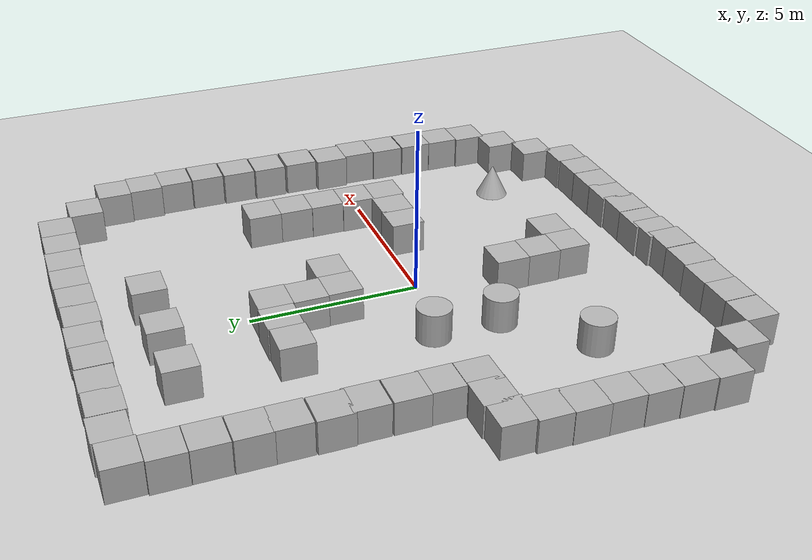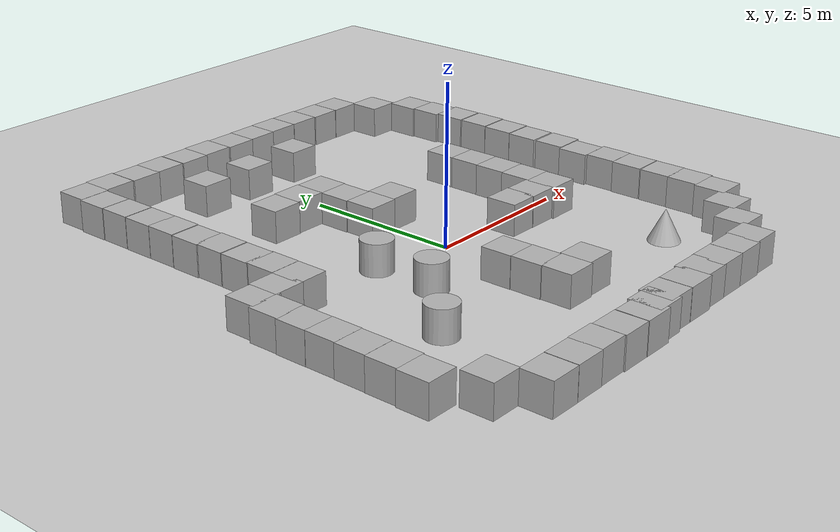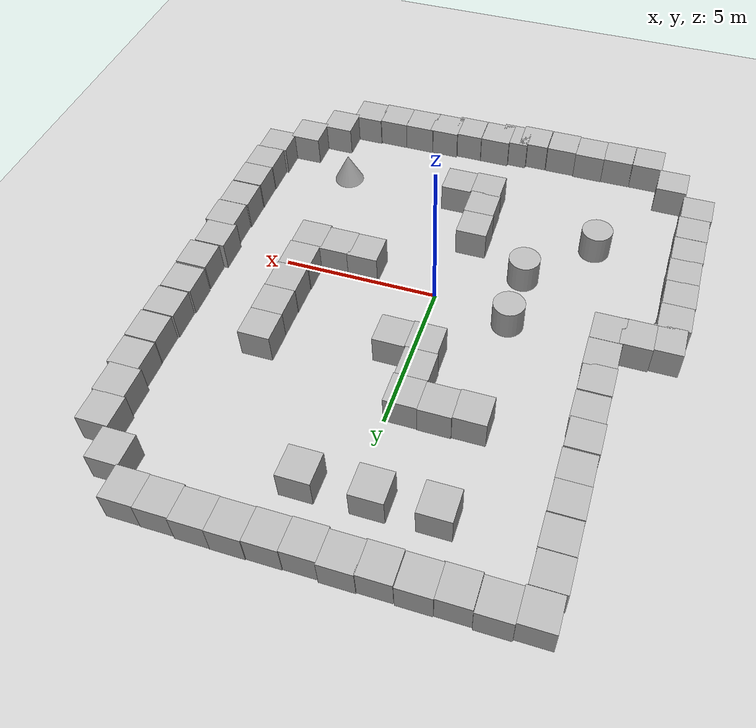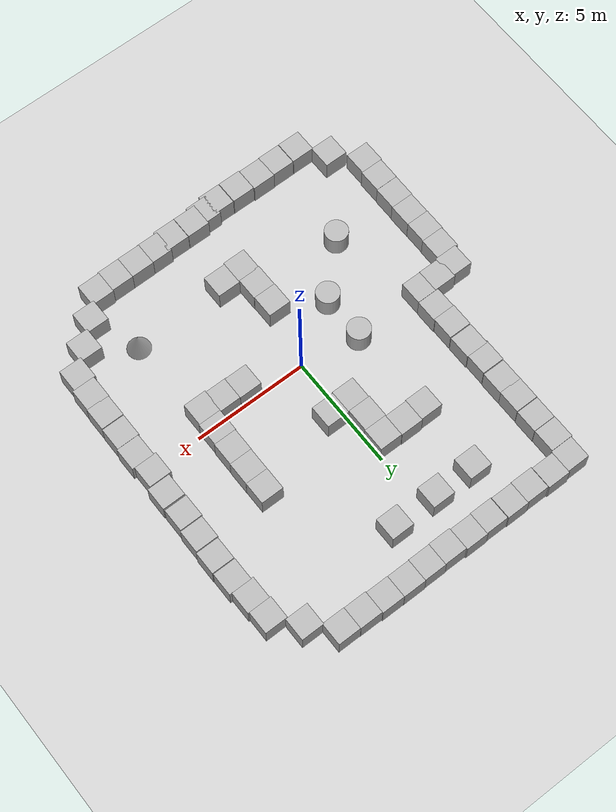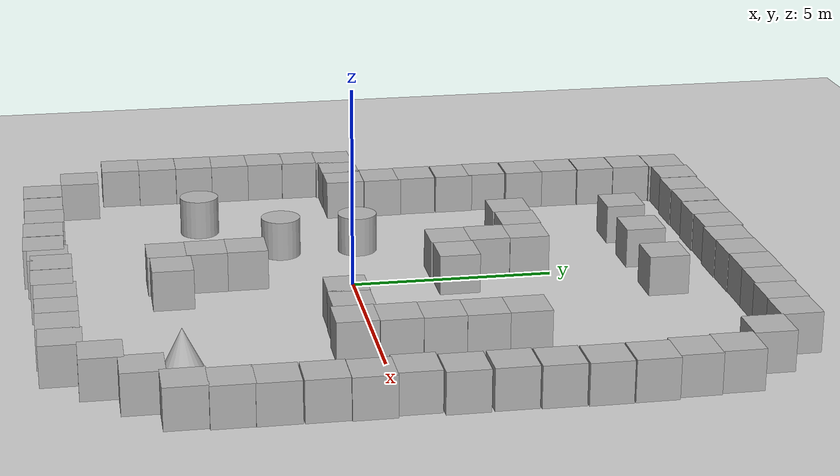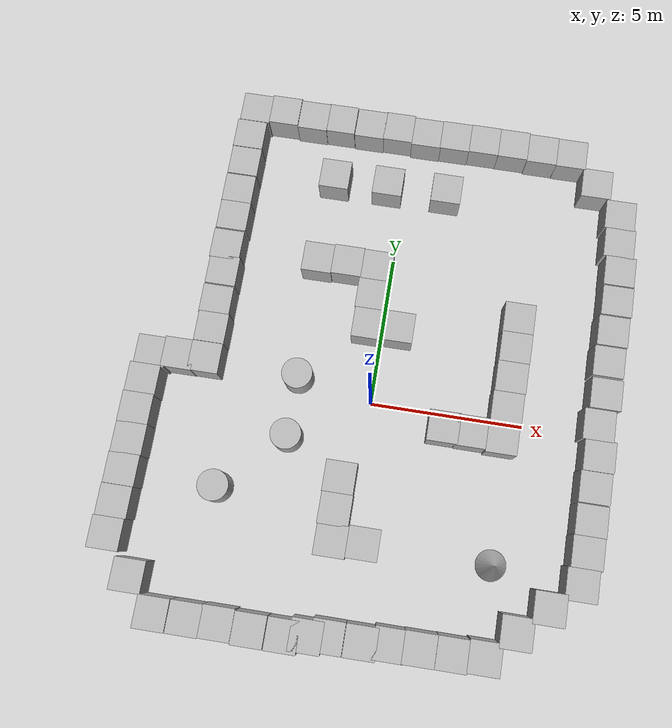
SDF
<sdf version='1.10'>
  <world name='empty'>
    <physics name='1ms' type='ode'>
      <max_step_size>0.10000000000000001</max_step_size>
      <real_time_factor>1</real_time_factor>
      <real_time_update_rate>1000</real_time_update_rate>
    </physics>
    <plugin name='gz::sim::systems::Physics' filename='gz-sim-physics-system'/>
    <plugin name='gz::sim::systems::UserCommands' filename='gz-sim-user-commands-system'/>
    <plugin name='gz::sim::systems::SceneBroadcaster' filename='gz-sim-scene-broadcaster-system'/>
    <plugin name='gz::sim::systems::Contact' filename='gz-sim-contact-system'/>
    <gravity>0 0 -9.8000000000000007</gravity>
    <magnetic_field>5.5644999999999998e-06 2.2875799999999999e-05 -4.2388400000000002e-05</magnetic_field>
    <atmosphere type='adiabatic'/>
    <scene>
      <ambient>0.400000006 0.400000006 0.400000006 1</ambient>
      <background>0.699999988 0.699999988 0.699999988 1</background>
      <shadows>true</shadows>
    </scene>
    <model name='ground_plane'>
      <static>true</static>
      <link name='link'>
        <collision name='collision'>
          <geometry>
            <plane>
              <normal>0 0 1</normal>
              <size>100 100</size>
            </plane>
          </geometry>
          <surface>
            <friction>
              <ode/>
            </friction>
            <bounce/>
            <contact/>
          </surface>
        </collision>
        <visual name='visual'>
          <geometry>
            <plane>
              <normal>0 0 1</normal>
              <size>100 100</size>
            </plane>
          </geometry>
          <material>
            <ambient>0.800000012 0.800000012 0.800000012 1</ambient>
            <diffuse>0.800000012 0.800000012 0.800000012 1</diffuse>
            <specular>0.800000012 0.800000012 0.800000012 1</specular>
          </material>
        </visual>
        <pose>0 0 0 0 0 0</pose>
        <inertial>
          <pose>0 0 0 0 0 0</pose>
          <mass>1</mass>
          <inertia>
            <ixx>1</ixx>
            <ixy>0</ixy>
            <ixz>0</ixz>
            <iyy>1</iyy>
            <iyz>0</iyz>
            <izz>1</izz>
          </inertia>
        </inertial>
        <enable_wind>false</enable_wind>
      </link>
      <pose>0 0 0 0 0 0</pose>
      <self_collide>false</self_collide>
    </model>
    <model name='box'>
      <pose>0.524736697470924 2.5003364620057273 0.49999999019606367 2.0528233015395709e-11 1.9476678967544364e-08 2.0088363631572271e-07</pose>
      <link name='box_link'>
        <inertial>
          <inertia>
            <ixx>0.16666</ixx>
            <ixy>0</ixy>
            <ixz>0</ixz>
            <iyy>0.16666</iyy>
            <iyz>0</iyz>
            <izz>0.16666</izz>
          </inertia>
          <mass>1</mass>
          <pose>0 0 0 0 0 0</pose>
        </inertial>
        <collision name='box_collision'>
          <geometry>
            <box>
              <size>1 1 1</size>
            </box>
          </geometry>
          <surface>
            <friction>
              <ode/>
            </friction>
            <bounce/>
            <contact/>
          </surface>
        </collision>
        <visual name='box_visual'>
          <geometry>
            <box>
              <size>1 1 1</size>
            </box>
          </geometry>
          <material>
            <ambient>0.300000012 0.300000012 0.300000012 1</ambient>
            <diffuse>0.699999988 0.699999988 0.699999988 1</diffuse>
            <specular>1 1 1 1</specular>
          </material>
        </visual>
        <pose>0 0 0 0 0 0</pose>
        <enable_wind>false</enable_wind>
      </link>
      <static>false</static>
      <self_collide>false</self_collide>
    </model>
    <model name='box_0'>
      <pose>-0.47526292159905265 2.4642455740105049 0.49999999019962665 9.8009418239771478e-09 -6.7491993512226618e-13 3.7354885587755947e-07</pose>
      <link name='box_link'>
        <inertial>
          <inertia>
            <ixx>0.16666</ixx>
            <ixy>0</ixy>
            <ixz>0</ixz>
            <iyy>0.16666</iyy>
            <iyz>0</iyz>
            <izz>0.16666</izz>
          </inertia>
          <mass>1</mass>
          <pose>0 0 0 0 0 0</pose>
        </inertial>
        <collision name='box_collision'>
          <geometry>
            <box>
              <size>1 1 1</size>
            </box>
          </geometry>
          <surface>
            <friction>
              <ode/>
            </friction>
            <bounce/>
            <contact/>
          </surface>
        </collision>
        <visual name='box_visual'>
          <geometry>
            <box>
              <size>1 1 1</size>
            </box>
          </geometry>
          <material>
            <ambient>0.300000012 0.300000012 0.300000012 1</ambient>
            <diffuse>0.699999988 0.699999988 0.699999988 1</diffuse>
            <specular>1 1 1 1</specular>
          </material>
        </visual>
        <pose>0 0 0 0 0 0</pose>
        <enable_wind>false</enable_wind>
      </link>
      <static>false</static>
      <self_collide>false</self_collide>
    </model>
    <model name='box_1'>
      <pose>-0.50301739909293941 3.4642451154851952 0.49999999019874231 -1.9580852355804939e-08 -1.1360315727130862e-12 3.8592032094083983e-07</pose>
      <link name='box_link'>
        <inertial>
          <inertia>
            <ixx>0.16666</ixx>
            <ixy>0</ixy>
            <ixz>0</ixz>
            <iyy>0.16666</iyy>
            <iyz>0</iyz>
            <izz>0.16666</izz>
          </inertia>
          <mass>1</mass>
          <pose>0 0 0 0 0 0</pose>
        </inertial>
        <collision name='box_collision'>
          <geometry>
            <box>
              <size>1 1 1</size>
            </box>
          </geometry>
          <surface>
            <friction>
              <ode/>
            </friction>
            <bounce/>
            <contact/>
          </surface>
        </collision>
        <visual name='box_visual'>
          <geometry>
            <box>
              <size>1 1 1</size>
            </box>
          </geometry>
          <material>
            <ambient>0.300000012 0.300000012 0.300000012 1</ambient>
            <diffuse>0.699999988 0.699999988 0.699999988 1</diffuse>
            <specular>1 1 1 1</specular>
          </material>
        </visual>
        <pose>0 0 0 0 0 0</pose>
        <enable_wind>false</enable_wind>
      </link>
      <static>false</static>
      <self_collide>false</self_collide>
    </model>
    <model name='cylinder'>
      <pose>-2.4787298964407922 0.47555413468499341 0.49999942638036005 1.8965155421226654e-19 3.0032176483774435e-19 -9.0381767484860335e-21</pose>
      <link name='cylinder_link'>
        <inertial>
          <inertia>
            <ixx>0.14580000000000001</ixx>
            <ixy>0</ixy>
            <ixz>0</ixz>
            <iyy>0.14580000000000001</iyy>
            <iyz>0</iyz>
            <izz>0.125</izz>
          </inertia>
          <mass>1</mass>
          <pose>0 0 0 0 0 0</pose>
        </inertial>
        <collision name='cylinder_collision'>
          <geometry>
            <cylinder>
              <radius>0.5</radius>
              <length>1</length>
            </cylinder>
          </geometry>
          <surface>
            <friction>
              <ode/>
            </friction>
            <bounce/>
            <contact/>
          </surface>
        </collision>
        <visual name='cylinder_visual'>
          <geometry>
            <cylinder>
              <radius>0.5</radius>
              <length>1</length>
            </cylinder>
          </geometry>
          <material>
            <ambient>0.300000012 0.300000012 0.300000012 1</ambient>
            <diffuse>0.699999988 0.699999988 0.699999988 1</diffuse>
            <specular>1 1 1 1</specular>
          </material>
        </visual>
        <pose>0 0 0 0 0 0</pose>
        <enable_wind>false</enable_wind>
      </link>
      <static>false</static>
      <self_collide>false</self_collide>
    </model>
    <model name='cylinder_0'>
      <pose>-2.4944941398360996 -1.5050460931617933 0.49999942638036005 -9.451208056923102e-20 4.300082519062569e-19 6.8155861792033474e-21</pose>
      <link name='cylinder_link'>
        <inertial>
          <inertia>
            <ixx>0.14580000000000001</ixx>
            <ixy>0</ixy>
            <ixz>0</ixz>
            <iyy>0.14580000000000001</iyy>
            <iyz>0</iyz>
            <izz>0.125</izz>
          </inertia>
          <mass>1</mass>
          <pose>0 0 0 0 0 0</pose>
        </inertial>
        <collision name='cylinder_collision'>
          <geometry>
            <cylinder>
              <radius>0.5</radius>
              <length>1</length>
            </cylinder>
          </geometry>
          <surface>
            <friction>
              <ode/>
            </friction>
            <bounce/>
            <contact/>
          </surface>
        </collision>
        <visual name='cylinder_visual'>
          <geometry>
            <cylinder>
              <radius>0.5</radius>
              <length>1</length>
            </cylinder>
          </geometry>
          <material>
            <ambient>0.300000012 0.300000012 0.300000012 1</ambient>
            <diffuse>0.699999988 0.699999988 0.699999988 1</diffuse>
            <specular>1 1 1 1</specular>
          </material>
        </visual>
        <pose>0 0 0 0 0 0</pose>
        <enable_wind>false</enable_wind>
      </link>
      <static>false</static>
      <self_collide>false</self_collide>
    </model>
    <model name='box_2'>
      <pose>-0.53410556503870477 -4.5478043600571363 0.4999999902278196 1.9656681869713402e-08 -1.1524613135909799e-10 6.3075753912477546e-07</pose>
      <link name='box_link'>
        <inertial>
          <inertia>
            <ixx>0.16666</ixx>
            <ixy>0</ixy>
            <ixz>0</ixz>
            <iyy>0.16666</iyy>
            <iyz>0</iyz>
            <izz>0.16666</izz>
          </inertia>
          <mass>1</mass>
          <pose>0 0 0 0 0 0</pose>
        </inertial>
        <collision name='box_collision'>
          <geometry>
            <box>
              <size>1 1 1</size>
            </box>
          </geometry>
          <surface>
            <friction>
              <ode/>
            </friction>
            <bounce/>
            <contact/>
          </surface>
        </collision>
        <visual name='box_visual'>
          <geometry>
            <box>
              <size>1 1 1</size>
            </box>
          </geometry>
          <material>
            <ambient>0.300000012 0.300000012 0.300000012 1</ambient>
            <diffuse>0.699999988 0.699999988 0.699999988 1</diffuse>
            <specular>1 1 1 1</specular>
          </material>
        </visual>
        <pose>0 0 0 0 0 0</pose>
        <enable_wind>false</enable_wind>
      </link>
      <static>false</static>
      <self_collide>false</self_collide>
    </model>
    <model name='box_3'>
      <pose>-0.56094903997092826 -3.5893649230956175 0.49999999020007962 -9.8027606147936074e-09 -6.8125787869436315e-13 1.5771510889533733e-07</pose>
      <link name='box_link'>
        <inertial>
          <inertia>
            <ixx>0.16666</ixx>
            <ixy>0</ixy>
            <ixz>0</ixz>
            <iyy>0.16666</iyy>
            <iyz>0</iyz>
            <izz>0.16666</izz>
          </inertia>
          <mass>1</mass>
          <pose>0 0 0 0 0 0</pose>
        </inertial>
        <collision name='box_collision'>
          <geometry>
            <box>
              <size>1 1 1</size>
            </box>
          </geometry>
          <surface>
            <friction>
              <ode/>
            </friction>
            <bounce/>
            <contact/>
          </surface>
        </collision>
        <visual name='box_visual'>
          <geometry>
            <box>
              <size>1 1 1</size>
            </box>
          </geometry>
          <material>
            <ambient>0.300000012 0.300000012 0.300000012 1</ambient>
            <diffuse>0.699999988 0.699999988 0.699999988 1</diffuse>
            <specular>1 1 1 1</specular>
          </material>
        </visual>
        <pose>0 0 0 0 0 0</pose>
        <enable_wind>false</enable_wind>
      </link>
      <static>false</static>
      <self_collide>false</self_collide>
    </model>
    <model name='box_4'>
      <pose>-0.57684420060578601 -2.5893643469614012 0.49999999019962799 -9.7985463552778233e-09 -6.7892859761239003e-13 1.8663244424998509e-07</pose>
      <link name='box_link'>
        <inertial>
          <inertia>
            <ixx>0.16666</ixx>
            <ixy>0</ixy>
            <ixz>0</ixz>
            <iyy>0.16666</iyy>
            <iyz>0</iyz>
            <izz>0.16666</izz>
          </inertia>
          <mass>1</mass>
          <pose>0 0 0 0 0 0</pose>
        </inertial>
        <collision name='box_collision'>
          <geometry>
            <box>
              <size>1 1 1</size>
            </box>
          </geometry>
          <surface>
            <friction>
              <ode/>
            </friction>
            <bounce/>
            <contact/>
          </surface>
        </collision>
        <visual name='box_visual'>
          <geometry>
            <box>
              <size>1 1 1</size>
            </box>
          </geometry>
          <material>
            <ambient>0.300000012 0.300000012 0.300000012 1</ambient>
            <diffuse>0.699999988 0.699999988 0.699999988 1</diffuse>
            <specular>1 1 1 1</specular>
          </material>
        </visual>
        <pose>0 0 0 0 0 0</pose>
        <enable_wind>false</enable_wind>
      </link>
      <static>false</static>
      <self_collide>false</self_collide>
    </model>
    <model name='box_5'>
      <pose>0.4658941225453252 -4.4876447452990105 0.49999999019677743 1.4045741384028449e-11 9.5892851848946801e-09 3.1991576014536165e-07</pose>
      <link name='box_link'>
        <inertial>
          <inertia>
            <ixx>0.16666</ixx>
            <ixy>0</ixy>
            <ixz>0</ixz>
            <iyy>0.16666</iyy>
            <iyz>0</iyz>
            <izz>0.16666</izz>
          </inertia>
          <mass>1</mass>
          <pose>0 0 0 0 0 0</pose>
        </inertial>
        <collision name='box_collision'>
          <geometry>
            <box>
              <size>1 1 1</size>
            </box>
          </geometry>
          <surface>
            <friction>
              <ode/>
            </friction>
            <bounce/>
            <contact/>
          </surface>
        </collision>
        <visual name='box_visual'>
          <geometry>
            <box>
              <size>1 1 1</size>
            </box>
          </geometry>
          <material>
            <ambient>0.300000012 0.300000012 0.300000012 1</ambient>
            <diffuse>0.699999988 0.699999988 0.699999988 1</diffuse>
            <specular>1 1 1 1</specular>
          </material>
        </visual>
        <pose>0 0 0 0 0 0</pose>
        <enable_wind>false</enable_wind>
      </link>
      <static>false</static>
      <self_collide>false</self_collide>
    </model>
    <model name='box_6'>
      <pose>2.4251415029204986 -0.51640693351667699 0.49999999020007807 8.0485426714338308e-12 -1.9603181426533481e-08 3.2495010891417823e-06</pose>
      <link name='box_link'>
        <inertial>
          <inertia>
            <ixx>0.16666</ixx>
            <ixy>0</ixy>
            <ixz>0</ixz>
            <iyy>0.16666</iyy>
            <iyz>0</iyz>
            <izz>0.16666</izz>
          </inertia>
          <mass>1</mass>
          <pose>0 0 0 0 0 0</pose>
        </inertial>
        <collision name='box_collision'>
          <geometry>
            <box>
              <size>1 1 1</size>
            </box>
          </geometry>
          <surface>
            <friction>
              <ode/>
            </friction>
            <bounce/>
            <contact/>
          </surface>
        </collision>
        <visual name='box_visual'>
          <geometry>
            <box>
              <size>1 1 1</size>
            </box>
          </geometry>
          <material>
            <ambient>0.300000012 0.300000012 0.300000012 1</ambient>
            <diffuse>0.699999988 0.699999988 0.699999988 1</diffuse>
            <specular>1 1 1 1</specular>
          </material>
        </visual>
        <pose>0 0 0 0 0 0</pose>
        <enable_wind>false</enable_wind>
      </link>
      <static>false</static>
      <self_collide>false</self_collide>
    </model>
    <model name='box_7'>
      <pose>3.3460310593011684 -0.53319752396077735 0.49999999020248048 5.8692967133810578e-12 -1.9552070684915997e-08 7.8408606438712837e-06</pose>
      <link name='box_link'>
        <inertial>
          <inertia>
            <ixx>0.16666</ixx>
            <ixy>0</ixy>
            <ixz>0</ixz>
            <iyy>0.16666</iyy>
            <iyz>0</iyz>
            <izz>0.16666</izz>
          </inertia>
          <mass>1</mass>
          <pose>0 0 0 0 0 0</pose>
        </inertial>
        <collision name='box_collision'>
          <geometry>
            <box>
              <size>1 1 1</size>
            </box>
          </geometry>
          <surface>
            <friction>
              <ode/>
            </friction>
            <bounce/>
            <contact/>
          </surface>
        </collision>
        <visual name='box_visual'>
          <geometry>
            <box>
              <size>1 1 1</size>
            </box>
          </geometry>
          <material>
            <ambient>0.300000012 0.300000012 0.300000012 1</ambient>
            <diffuse>0.699999988 0.699999988 0.699999988 1</diffuse>
            <specular>1 1 1 1</specular>
          </material>
        </visual>
        <pose>0 0 0 0 0 0</pose>
        <enable_wind>false</enable_wind>
      </link>
      <static>false</static>
      <self_collide>false</self_collide>
    </model>
    <model name='box_8'>
      <pose>4.3155791228577778 -0.59553698079366979 0.49999999241762805 8.8830215002089552e-09 2.401707876268193e-08 2.4836349063779638e-05</pose>
      <link name='box_link'>
        <inertial>
          <inertia>
            <ixx>0.16666</ixx>
            <ixy>0</ixy>
            <ixz>0</ixz>
            <iyy>0.16666</iyy>
            <iyz>0</iyz>
            <izz>0.16666</izz>
          </inertia>
          <mass>1</mass>
          <pose>0 0 0 0 0 0</pose>
        </inertial>
        <collision name='box_collision'>
          <geometry>
            <box>
              <size>1 1 1</size>
            </box>
          </geometry>
          <surface>
            <friction>
              <ode/>
            </friction>
            <bounce/>
            <contact/>
          </surface>
        </collision>
        <visual name='box_visual'>
          <geometry>
            <box>
              <size>1 1 1</size>
            </box>
          </geometry>
          <material>
            <ambient>0.300000012 0.300000012 0.300000012 1</ambient>
            <diffuse>0.699999988 0.699999988 0.699999988 1</diffuse>
            <specular>1 1 1 1</specular>
          </material>
        </visual>
        <pose>0 0 0 0 0 0</pose>
        <enable_wind>false</enable_wind>
      </link>
      <static>false</static>
      <self_collide>false</self_collide>
    </model>
    <model name='box_9'>
      <pose>4.3448509277562826 0.40446374225777043 0.49999999211979645 7.6734533011678575e-09 2.3426084460918485e-08 2.4846498721593773e-05</pose>
      <link name='box_link'>
        <inertial>
          <inertia>
            <ixx>0.16666</ixx>
            <ixy>0</ixy>
            <ixz>0</ixz>
            <iyy>0.16666</iyy>
            <iyz>0</iyz>
            <izz>0.16666</izz>
          </inertia>
          <mass>1</mass>
          <pose>0 0 0 0 0 0</pose>
        </inertial>
        <collision name='box_collision'>
          <geometry>
            <box>
              <size>1 1 1</size>
            </box>
          </geometry>
          <surface>
            <friction>
              <ode/>
            </friction>
            <bounce/>
            <contact/>
          </surface>
        </collision>
        <visual name='box_visual'>
          <geometry>
            <box>
              <size>1 1 1</size>
            </box>
          </geometry>
          <material>
            <ambient>0.300000012 0.300000012 0.300000012 1</ambient>
            <diffuse>0.699999988 0.699999988 0.699999988 1</diffuse>
            <specular>1 1 1 1</specular>
          </material>
        </visual>
        <pose>0 0 0 0 0 0</pose>
        <enable_wind>false</enable_wind>
      </link>
      <static>false</static>
      <self_collide>false</self_collide>
    </model>
    <model name='box_10'>
      <pose>4.3671556992405156 1.4044653718104809 0.49999999020050911 -1.4066092948692165e-08 4.1759308201097749e-12 2.3038047252878038e-05</pose>
      <link name='box_link'>
        <inertial>
          <inertia>
            <ixx>0.16666</ixx>
            <ixy>0</ixy>
            <ixz>0</ixz>
            <iyy>0.16666</iyy>
            <iyz>0</iyz>
            <izz>0.16666</izz>
          </inertia>
          <mass>1</mass>
          <pose>0 0 0 0 0 0</pose>
        </inertial>
        <collision name='box_collision'>
          <geometry>
            <box>
              <size>1 1 1</size>
            </box>
          </geometry>
          <surface>
            <friction>
              <ode/>
            </friction>
            <bounce/>
            <contact/>
          </surface>
        </collision>
        <visual name='box_visual'>
          <geometry>
            <box>
              <size>1 1 1</size>
            </box>
          </geometry>
          <material>
            <ambient>0.300000012 0.300000012 0.300000012 1</ambient>
            <diffuse>0.699999988 0.699999988 0.699999988 1</diffuse>
            <specular>1 1 1 1</specular>
          </material>
        </visual>
        <pose>0 0 0 0 0 0</pose>
        <enable_wind>false</enable_wind>
      </link>
      <static>false</static>
      <self_collide>false</self_collide>
    </model>
    <model name='box_11'>
      <pose>4.3795451639200085 2.4044762643899475 0.49999999020802821 1.9617229519158874e-08 8.1122862833365634e-11 2.9883756320125841e-07</pose>
      <link name='box_link'>
        <inertial>
          <inertia>
            <ixx>0.16666</ixx>
            <ixy>0</ixy>
            <ixz>0</ixz>
            <iyy>0.16666</iyy>
            <iyz>0</iyz>
            <izz>0.16666</izz>
          </inertia>
          <mass>1</mass>
          <pose>0 0 0 0 0 0</pose>
        </inertial>
        <collision name='box_collision'>
          <geometry>
            <box>
              <size>1 1 1</size>
            </box>
          </geometry>
          <surface>
            <friction>
              <ode/>
            </friction>
            <bounce/>
            <contact/>
          </surface>
        </collision>
        <visual name='box_visual'>
          <geometry>
            <box>
              <size>1 1 1</size>
            </box>
          </geometry>
          <material>
            <ambient>0.300000012 0.300000012 0.300000012 1</ambient>
            <diffuse>0.699999988 0.699999988 0.699999988 1</diffuse>
            <specular>1 1 1 1</specular>
          </material>
        </visual>
        <pose>0 0 0 0 0 0</pose>
        <enable_wind>false</enable_wind>
      </link>
      <static>false</static>
      <self_collide>false</self_collide>
    </model>
    <model name='box_12'>
      <pose>4.3763141297772838 3.3954105433026451 0.4999999901911259 -1.9559917834768265e-08 -7.3646884846316932e-12 5.846187059106633e-07</pose>
      <link name='box_link'>
        <inertial>
          <inertia>
            <ixx>0.16666</ixx>
            <ixy>0</ixy>
            <ixz>0</ixz>
            <iyy>0.16666</iyy>
            <iyz>0</iyz>
            <izz>0.16666</izz>
          </inertia>
          <mass>1</mass>
          <pose>0 0 0 0 0 0</pose>
        </inertial>
        <collision name='box_collision'>
          <geometry>
            <box>
              <size>1 1 1</size>
            </box>
          </geometry>
          <surface>
            <friction>
              <ode/>
            </friction>
            <bounce/>
            <contact/>
          </surface>
        </collision>
        <visual name='box_visual'>
          <geometry>
            <box>
              <size>1 1 1</size>
            </box>
          </geometry>
          <material>
            <ambient>0.300000012 0.300000012 0.300000012 1</ambient>
            <diffuse>0.699999988 0.699999988 0.699999988 1</diffuse>
            <specular>1 1 1 1</specular>
          </material>
        </visual>
        <pose>0 0 0 0 0 0</pose>
        <enable_wind>false</enable_wind>
      </link>
      <static>false</static>
      <self_collide>false</self_collide>
    </model>
    <model name='box_13'>
      <pose>3.4785942979263873 9.4888861230913797 0.49999999019871588 2.5021919377943448e-12 3.9188327872326739e-09 -2.7722733610105434e-07</pose>
      <link name='box_link'>
        <inertial>
          <inertia>
            <ixx>0.16666</ixx>
            <ixy>0</ixy>
            <ixz>0</ixz>
            <iyy>0.16666</iyy>
            <iyz>0</iyz>
            <izz>0.16666</izz>
          </inertia>
          <mass>1</mass>
          <pose>0 0 0 0 0 0</pose>
        </inertial>
        <collision name='box_collision'>
          <geometry>
            <box>
              <size>1 1 1</size>
            </box>
          </geometry>
          <surface>
            <friction>
              <ode/>
            </friction>
            <bounce/>
            <contact/>
          </surface>
        </collision>
        <visual name='box_visual'>
          <geometry>
            <box>
              <size>1 1 1</size>
            </box>
          </geometry>
          <material>
            <ambient>0.300000012 0.300000012 0.300000012 1</ambient>
            <diffuse>0.699999988 0.699999988 0.699999988 1</diffuse>
            <specular>1 1 1 1</specular>
          </material>
        </visual>
        <pose>0 0 0 0 0 0</pose>
        <enable_wind>false</enable_wind>
      </link>
      <static>false</static>
      <self_collide>false</self_collide>
    </model>
    <model name='box_14'>
      <pose>2.4785947645034661 9.4966416109474334 0.49999999018475866 -7.4069138696486001e-12 -9.4172170422715719e-09 -3.2357303575100427e-07</pose>
      <link name='box_link'>
        <inertial>
          <inertia>
            <ixx>0.16666</ixx>
            <ixy>0</ixy>
            <ixz>0</ixz>
            <iyy>0.16666</iyy>
            <iyz>0</iyz>
            <izz>0.16666</izz>
          </inertia>
          <mass>1</mass>
          <pose>0 0 0 0 0 0</pose>
        </inertial>
        <collision name='box_collision'>
          <geometry>
            <box>
              <size>1 1 1</size>
            </box>
          </geometry>
          <surface>
            <friction>
              <ode/>
            </friction>
            <bounce/>
            <contact/>
          </surface>
        </collision>
        <visual name='box_visual'>
          <geometry>
            <box>
              <size>1 1 1</size>
            </box>
          </geometry>
          <material>
            <ambient>0.300000012 0.300000012 0.300000012 1</ambient>
            <diffuse>0.699999988 0.699999988 0.699999988 1</diffuse>
            <specular>1 1 1 1</specular>
          </material>
        </visual>
        <pose>0 0 0 0 0 0</pose>
        <enable_wind>false</enable_wind>
      </link>
      <static>false</static>
      <self_collide>false</self_collide>
    </model>
    <model name='box_15'>
      <pose>4.4785942478098235 9.4492298926478089 0.49999999019985397 -6.7571858887571462e-13 4.1093077161975367e-09 -2.8177229611897375e-07</pose>
      <link name='box_link'>
        <inertial>
          <inertia>
            <ixx>0.16666</ixx>
            <ixy>0</ixy>
            <ixz>0</ixz>
            <iyy>0.16666</iyy>
            <iyz>0</iyz>
            <izz>0.16666</izz>
          </inertia>
          <mass>1</mass>
          <pose>0 0 0 0 0 0</pose>
        </inertial>
        <collision name='box_collision'>
          <geometry>
            <box>
              <size>1 1 1</size>
            </box>
          </geometry>
          <surface>
            <friction>
              <ode/>
            </friction>
            <bounce/>
            <contact/>
          </surface>
        </collision>
        <visual name='box_visual'>
          <geometry>
            <box>
              <size>1 1 1</size>
            </box>
          </geometry>
          <material>
            <ambient>0.300000012 0.300000012 0.300000012 1</ambient>
            <diffuse>0.699999988 0.699999988 0.699999988 1</diffuse>
            <specular>1 1 1 1</specular>
          </material>
        </visual>
        <pose>0 0 0 0 0 0</pose>
        <enable_wind>false</enable_wind>
      </link>
      <static>false</static>
      <self_collide>false</self_collide>
    </model>
    <model name='box_16'>
      <pose>5.4785943355100919 9.4350745346117506 0.49999999019984021 -6.7968710803913345e-13 3.921492205411589e-09 -2.7817858854219567e-07</pose>
      <link name='box_link'>
        <inertial>
          <inertia>
            <ixx>0.16666</ixx>
            <ixy>0</ixy>
            <ixz>0</ixz>
            <iyy>0.16666</iyy>
            <iyz>0</iyz>
            <izz>0.16666</izz>
          </inertia>
          <mass>1</mass>
          <pose>0 0 0 0 0 0</pose>
        </inertial>
        <collision name='box_collision'>
          <geometry>
            <box>
              <size>1 1 1</size>
            </box>
          </geometry>
          <surface>
            <friction>
              <ode/>
            </friction>
            <bounce/>
            <contact/>
          </surface>
        </collision>
        <visual name='box_visual'>
          <geometry>
            <box>
              <size>1 1 1</size>
            </box>
          </geometry>
          <material>
            <ambient>0.300000012 0.300000012 0.300000012 1</ambient>
            <diffuse>0.699999988 0.699999988 0.699999988 1</diffuse>
            <specular>1 1 1 1</specular>
          </material>
        </visual>
        <pose>0 0 0 0 0 0</pose>
        <enable_wind>false</enable_wind>
      </link>
      <static>false</static>
      <self_collide>false</self_collide>
    </model>
    <model name='box_17'>
      <pose>1.4785951337053422 9.4799652610031853 0.49999999019994373 -1.5249625503558359e-13 -1.3422235593269671e-08 -1.7206307201443844e-07</pose>
      <link name='box_link'>
        <inertial>
          <inertia>
            <ixx>0.16666</ixx>
            <ixy>0</ixy>
            <ixz>0</ixz>
            <iyy>0.16666</iyy>
            <iyz>0</iyz>
            <izz>0.16666</izz>
          </inertia>
          <mass>1</mass>
          <pose>0 0 0 0 0 0</pose>
        </inertial>
        <collision name='box_collision'>
          <geometry>
            <box>
              <size>1 1 1</size>
            </box>
          </geometry>
          <surface>
            <friction>
              <ode/>
            </friction>
            <bounce/>
            <contact/>
          </surface>
        </collision>
        <visual name='box_visual'>
          <geometry>
            <box>
              <size>1 1 1</size>
            </box>
          </geometry>
          <material>
            <ambient>0.300000012 0.300000012 0.300000012 1</ambient>
            <diffuse>0.699999988 0.699999988 0.699999988 1</diffuse>
            <specular>1 1 1 1</specular>
          </material>
        </visual>
        <pose>0 0 0 0 0 0</pose>
        <enable_wind>false</enable_wind>
      </link>
      <static>false</static>
      <self_collide>false</self_collide>
    </model>
    <model name='box_18'>
      <pose>0.50157591497799403 9.462697623218169 0.49999999020114666 -1.7186061489472927e-11 -1.9601732241907378e-08 -4.8818517006823555e-08</pose>
      <link name='box_link'>
        <inertial>
          <inertia>
            <ixx>0.16666</ixx>
            <ixy>0</ixy>
            <ixz>0</ixz>
            <iyy>0.16666</iyy>
            <iyz>0</iyz>
            <izz>0.16666</izz>
          </inertia>
          <mass>1</mass>
          <pose>0 0 0 0 0 0</pose>
        </inertial>
        <collision name='box_collision'>
          <geometry>
            <box>
              <size>1 1 1</size>
            </box>
          </geometry>
          <surface>
            <friction>
              <ode/>
            </friction>
            <bounce/>
            <contact/>
          </surface>
        </collision>
        <visual name='box_visual'>
          <geometry>
            <box>
              <size>1 1 1</size>
            </box>
          </geometry>
          <material>
            <ambient>0.300000012 0.300000012 0.300000012 1</ambient>
            <diffuse>0.699999988 0.699999988 0.699999988 1</diffuse>
            <specular>1 1 1 1</specular>
          </material>
        </visual>
        <pose>0 0 0 0 0 0</pose>
        <enable_wind>false</enable_wind>
      </link>
      <static>false</static>
      <self_collide>false</self_collide>
    </model>
    <model name='box_19'>
      <pose>-0.49842404471039115 9.5155142121650851 0.49999999019966845 3.8528456052840277e-12 -1.9596778538986776e-08 -4.8997244930443475e-08</pose>
      <link name='box_link'>
        <inertial>
          <inertia>
            <ixx>0.16666</ixx>
            <ixy>0</ixy>
            <ixz>0</ixz>
            <iyy>0.16666</iyy>
            <iyz>0</iyz>
            <izz>0.16666</izz>
          </inertia>
          <mass>1</mass>
          <pose>0 0 0 0 0 0</pose>
        </inertial>
        <collision name='box_collision'>
          <geometry>
            <box>
              <size>1 1 1</size>
            </box>
          </geometry>
          <surface>
            <friction>
              <ode/>
            </friction>
            <bounce/>
            <contact/>
          </surface>
        </collision>
        <visual name='box_visual'>
          <geometry>
            <box>
              <size>1 1 1</size>
            </box>
          </geometry>
          <material>
            <ambient>0.300000012 0.300000012 0.300000012 1</ambient>
            <diffuse>0.699999988 0.699999988 0.699999988 1</diffuse>
            <specular>1 1 1 1</specular>
          </material>
        </visual>
        <pose>0 0 0 0 0 0</pose>
        <enable_wind>false</enable_wind>
      </link>
      <static>false</static>
      <self_collide>false</self_collide>
    </model>
    <model name='box_20'>
      <pose>-1.4742271035418915 9.4912127328169777 0.49999999020099106 -9.7895765620471089e-12 -1.9604668503276315e-08 -4.5569773364331932e-07</pose>
      <link name='box_link'>
        <inertial>
          <inertia>
            <ixx>0.16666</ixx>
            <ixy>0</ixy>
            <ixz>0</ixz>
            <iyy>0.16666</iyy>
            <iyz>0</iyz>
            <izz>0.16666</izz>
          </inertia>
          <mass>1</mass>
          <pose>0 0 0 0 0 0</pose>
        </inertial>
        <collision name='box_collision'>
          <geometry>
            <box>
              <size>1 1 1</size>
            </box>
          </geometry>
          <surface>
            <friction>
              <ode/>
            </friction>
            <bounce/>
            <contact/>
          </surface>
        </collision>
        <visual name='box_visual'>
          <geometry>
            <box>
              <size>1 1 1</size>
            </box>
          </geometry>
          <material>
            <ambient>0.300000012 0.300000012 0.300000012 1</ambient>
            <diffuse>0.699999988 0.699999988 0.699999988 1</diffuse>
            <specular>1 1 1 1</specular>
          </material>
        </visual>
        <pose>0 0 0 0 0 0</pose>
        <enable_wind>false</enable_wind>
      </link>
      <static>false</static>
      <self_collide>false</self_collide>
    </model>
    <model name='box_21'>
      <pose>-0.47622361684656467 4.4642449989606847 0.49999999019962521 -1.4461815439606481e-08 2.177274633007747e-13 7.225565463141998e-08</pose>
      <link name='box_link'>
        <inertial>
          <inertia>
            <ixx>0.16666</ixx>
            <ixy>0</ixy>
            <ixz>0</ixz>
            <iyy>0.16666</iyy>
            <iyz>0</iyz>
            <izz>0.16666</izz>
          </inertia>
          <mass>1</mass>
          <pose>0 0 0 0 0 0</pose>
        </inertial>
        <collision name='box_collision'>
          <geometry>
            <box>
              <size>1 1 1</size>
            </box>
          </geometry>
          <surface>
            <friction>
              <ode/>
            </friction>
            <bounce/>
            <contact/>
          </surface>
        </collision>
        <visual name='box_visual'>
          <geometry>
            <box>
              <size>1 1 1</size>
            </box>
          </geometry>
          <material>
            <ambient>0.300000012 0.300000012 0.300000012 1</ambient>
            <diffuse>0.699999988 0.699999988 0.699999988 1</diffuse>
            <specular>1 1 1 1</specular>
          </material>
        </visual>
        <pose>0 0 0 0 0 0</pose>
        <enable_wind>false</enable_wind>
      </link>
      <static>false</static>
      <self_collide>false</self_collide>
    </model>
    <model name='box_22'>
      <pose>-1.4762231323036259 4.4839882101311641 0.5000001020282927 -7.6125261166845615e-10 2.3789208539099318e-07 -2.6386814999145798e-08</pose>
      <link name='box_link'>
        <inertial>
          <inertia>
            <ixx>0.16666</ixx>
            <ixy>0</ixy>
            <ixz>0</ixz>
            <iyy>0.16666</iyy>
            <iyz>0</iyz>
            <izz>0.16666</izz>
          </inertia>
          <mass>1</mass>
          <pose>0 0 0 0 0 0</pose>
        </inertial>
        <collision name='box_collision'>
          <geometry>
            <box>
              <size>1 1 1</size>
            </box>
          </geometry>
          <surface>
            <friction>
              <ode/>
            </friction>
            <bounce/>
            <contact/>
          </surface>
        </collision>
        <visual name='box_visual'>
          <geometry>
            <box>
              <size>1 1 1</size>
            </box>
          </geometry>
          <material>
            <ambient>0.300000012 0.300000012 0.300000012 1</ambient>
            <diffuse>0.699999988 0.699999988 0.699999988 1</diffuse>
            <specular>1 1 1 1</specular>
          </material>
        </visual>
        <pose>0 0 0 0 0 0</pose>
        <enable_wind>false</enable_wind>
      </link>
      <static>false</static>
      <self_collide>false</self_collide>
    </model>
    <model name='box_23'>
      <pose>-2.4929506777758581 9.5168052536606726 0.49999999019955771 -7.453748859052733e-13 1.9599126148115115e-08 -1.7627971582793917e-08</pose>
      <link name='box_link'>
        <inertial>
          <inertia>
            <ixx>0.16666</ixx>
            <ixy>0</ixy>
            <ixz>0</ixz>
            <iyy>0.16666</iyy>
            <iyz>0</iyz>
            <izz>0.16666</izz>
          </inertia>
          <mass>1</mass>
          <pose>0 0 0 0 0 0</pose>
        </inertial>
        <collision name='box_collision'>
          <geometry>
            <box>
              <size>1 1 1</size>
            </box>
          </geometry>
          <surface>
            <friction>
              <ode/>
            </friction>
            <bounce/>
            <contact/>
          </surface>
        </collision>
        <visual name='box_visual'>
          <geometry>
            <box>
              <size>1 1 1</size>
            </box>
          </geometry>
          <material>
            <ambient>0.300000012 0.300000012 0.300000012 1</ambient>
            <diffuse>0.699999988 0.699999988 0.699999988 1</diffuse>
            <specular>1 1 1 1</specular>
          </material>
        </visual>
        <pose>0 0 0 0 0 0</pose>
        <enable_wind>false</enable_wind>
      </link>
      <static>false</static>
      <self_collide>false</self_collide>
    </model>
    <model name='box_24'>
      <pose>-3.4609139751847557 9.4959633999755457 0.49999999020047681 1.6362069076355865e-12 -1.9600981089067922e-08 -4.6286526147339579e-07</pose>
      <link name='box_link'>
        <inertial>
          <inertia>
            <ixx>0.16666</ixx>
            <ixy>0</ixy>
            <ixz>0</ixz>
            <iyy>0.16666</iyy>
            <iyz>0</iyz>
            <izz>0.16666</izz>
          </inertia>
          <mass>1</mass>
          <pose>0 0 0 0 0 0</pose>
        </inertial>
        <collision name='box_collision'>
          <geometry>
            <box>
              <size>1 1 1</size>
            </box>
          </geometry>
          <surface>
            <friction>
              <ode/>
            </friction>
            <bounce/>
            <contact/>
          </surface>
        </collision>
        <visual name='box_visual'>
          <geometry>
            <box>
              <size>1 1 1</size>
            </box>
          </geometry>
          <material>
            <ambient>0.300000012 0.300000012 0.300000012 1</ambient>
            <diffuse>0.699999988 0.699999988 0.699999988 1</diffuse>
            <specular>1 1 1 1</specular>
          </material>
        </visual>
        <pose>0 0 0 0 0 0</pose>
        <enable_wind>false</enable_wind>
      </link>
      <static>false</static>
      <self_collide>false</self_collide>
    </model>
    <model name='box_25'>
      <pose>-4.4728117546722723 9.542798497343048 0.49999999019962665 -2.2712539612192383e-13 8.352600245621544e-09 2.0626419607356885e-09</pose>
      <link name='box_link'>
        <inertial>
          <inertia>
            <ixx>0.16666</ixx>
            <ixy>0</ixy>
            <ixz>0</ixz>
            <iyy>0.16666</iyy>
            <iyz>0</iyz>
            <izz>0.16666</izz>
          </inertia>
          <mass>1</mass>
          <pose>0 0 0 0 0 0</pose>
        </inertial>
        <collision name='box_collision'>
          <geometry>
            <box>
              <size>1 1 1</size>
            </box>
          </geometry>
          <surface>
            <friction>
              <ode/>
            </friction>
            <bounce/>
            <contact/>
          </surface>
        </collision>
        <visual name='box_visual'>
          <geometry>
            <box>
              <size>1 1 1</size>
            </box>
          </geometry>
          <material>
            <ambient>0.300000012 0.300000012 0.300000012 1</ambient>
            <diffuse>0.699999988 0.699999988 0.699999988 1</diffuse>
            <specular>1 1 1 1</specular>
          </material>
        </visual>
        <pose>0 0 0 0 0 0</pose>
        <enable_wind>false</enable_wind>
      </link>
      <static>false</static>
      <self_collide>false</self_collide>
    </model>
    <model name='box_26'>
      <pose>-5.4728114347913692 9.4906921811964438 0.4999999914610786 2.2767488867195718e-13 -8.3779736211777681e-09 2.0830650656288485e-09</pose>
      <link name='box_link'>
        <inertial>
          <inertia>
            <ixx>0.16666</ixx>
            <ixy>0</ixy>
            <ixz>0</ixz>
            <iyy>0.16666</iyy>
            <iyz>0</iyz>
            <izz>0.16666</izz>
          </inertia>
          <mass>1</mass>
          <pose>0 0 0 0 0 0</pose>
        </inertial>
        <collision name='box_collision'>
          <geometry>
            <box>
              <size>1 1 1</size>
            </box>
          </geometry>
          <surface>
            <friction>
              <ode/>
            </friction>
            <bounce/>
            <contact/>
          </surface>
        </collision>
        <visual name='box_visual'>
          <geometry>
            <box>
              <size>1 1 1</size>
            </box>
          </geometry>
          <material>
            <ambient>0.300000012 0.300000012 0.300000012 1</ambient>
            <diffuse>0.699999988 0.699999988 0.699999988 1</diffuse>
            <specular>1 1 1 1</specular>
          </material>
        </visual>
        <pose>0 0 0 0 0 0</pose>
        <enable_wind>false</enable_wind>
      </link>
      <static>false</static>
      <self_collide>false</self_collide>
    </model>
    <model name='box_27'>
      <pose>-5.5258745283655175 8.4822873289778293 0.49999999990199806 2.163106304372845e-21 -1.6560291693952328e-21 2.2452215946946745e-23</pose>
      <link name='box_link'>
        <inertial>
          <inertia>
            <ixx>0.16666</ixx>
            <ixy>0</ixy>
            <ixz>0</ixz>
            <iyy>0.16666</iyy>
            <iyz>0</iyz>
            <izz>0.16666</izz>
          </inertia>
          <mass>1</mass>
          <pose>0 0 0 0 0 0</pose>
        </inertial>
        <collision name='box_collision'>
          <geometry>
            <box>
              <size>1 1 1</size>
            </box>
          </geometry>
          <surface>
            <friction>
              <ode/>
            </friction>
            <bounce/>
            <contact/>
          </surface>
        </collision>
        <visual name='box_visual'>
          <geometry>
            <box>
              <size>1 1 1</size>
            </box>
          </geometry>
          <material>
            <ambient>0.300000012 0.300000012 0.300000012 1</ambient>
            <diffuse>0.699999988 0.699999988 0.699999988 1</diffuse>
            <specular>1 1 1 1</specular>
          </material>
        </visual>
        <pose>0 0 0 0 0 0</pose>
        <enable_wind>false</enable_wind>
      </link>
      <static>false</static>
      <self_collide>false</self_collide>
    </model>
    <model name='box_28'>
      <pose>-5.517485968973352 7.4699410133515993 0.49999999990199806 2.163106304372845e-21 -1.6560291693952328e-21 2.2452215946946745e-23</pose>
      <link name='box_link'>
        <inertial>
          <inertia>
            <ixx>0.16666</ixx>
            <ixy>0</ixy>
            <ixz>0</ixz>
            <iyy>0.16666</iyy>
            <iyz>0</iyz>
            <izz>0.16666</izz>
          </inertia>
          <mass>1</mass>
          <pose>0 0 0 0 0 0</pose>
        </inertial>
        <collision name='box_collision'>
          <geometry>
            <box>
              <size>1 1 1</size>
            </box>
          </geometry>
          <surface>
            <friction>
              <ode/>
            </friction>
            <bounce/>
            <contact/>
          </surface>
        </collision>
        <visual name='box_visual'>
          <geometry>
            <box>
              <size>1 1 1</size>
            </box>
          </geometry>
          <material>
            <ambient>0.300000012 0.300000012 0.300000012 1</ambient>
            <diffuse>0.699999988 0.699999988 0.699999988 1</diffuse>
            <specular>1 1 1 1</specular>
          </material>
        </visual>
        <pose>0 0 0 0 0 0</pose>
        <enable_wind>false</enable_wind>
      </link>
      <static>false</static>
      <self_collide>false</self_collide>
    </model>
    <model name='box_29'>
      <pose>-5.5276196068390799 6.4439587581969944 0.49999999020075725 -1.9457309302596409e-08 -8.2510369569541207e-13 -1.7318396300007975e-07</pose>
      <link name='box_link'>
        <inertial>
          <inertia>
            <ixx>0.16666</ixx>
            <ixy>0</ixy>
            <ixz>0</ixz>
            <iyy>0.16666</iyy>
            <iyz>0</iyz>
            <izz>0.16666</izz>
          </inertia>
          <mass>1</mass>
          <pose>0 0 0 0 0 0</pose>
        </inertial>
        <collision name='box_collision'>
          <geometry>
            <box>
              <size>1 1 1</size>
            </box>
          </geometry>
          <surface>
            <friction>
              <ode/>
            </friction>
            <bounce/>
            <contact/>
          </surface>
        </collision>
        <visual name='box_visual'>
          <geometry>
            <box>
              <size>1 1 1</size>
            </box>
          </geometry>
          <material>
            <ambient>0.300000012 0.300000012 0.300000012 1</ambient>
            <diffuse>0.699999988 0.699999988 0.699999988 1</diffuse>
            <specular>1 1 1 1</specular>
          </material>
        </visual>
        <pose>0 0 0 0 0 0</pose>
        <enable_wind>false</enable_wind>
      </link>
      <static>false</static>
      <self_collide>false</self_collide>
    </model>
    <model name='box_30'>
      <pose>-5.5223616253347041 5.471669454354207 0.49999999021913916 1.9639456774705976e-08 1.3119336727615174e-10 3.0800938336529582e-07</pose>
      <link name='box_link'>
        <inertial>
          <inertia>
            <ixx>0.16666</ixx>
            <ixy>0</ixy>
            <ixz>0</ixz>
            <iyy>0.16666</iyy>
            <iyz>0</iyz>
            <izz>0.16666</izz>
          </inertia>
          <mass>1</mass>
          <pose>0 0 0 0 0 0</pose>
        </inertial>
        <collision name='box_collision'>
          <geometry>
            <box>
              <size>1 1 1</size>
            </box>
          </geometry>
          <surface>
            <friction>
              <ode/>
            </friction>
            <bounce/>
            <contact/>
          </surface>
        </collision>
        <visual name='box_visual'>
          <geometry>
            <box>
              <size>1 1 1</size>
            </box>
          </geometry>
          <material>
            <ambient>0.300000012 0.300000012 0.300000012 1</ambient>
            <diffuse>0.699999988 0.699999988 0.699999988 1</diffuse>
            <specular>1 1 1 1</specular>
          </material>
        </visual>
        <pose>0 0 0 0 0 0</pose>
        <enable_wind>false</enable_wind>
      </link>
      <static>false</static>
      <self_collide>false</self_collide>
    </model>
    <model name='box_31'>
      <pose>-5.5089277593279906 3.5174007969727259 0.49999999990199806 -2.052788585189231e-21 7.9840368278892396e-22 1.4978535966898781e-22</pose>
      <link name='box_link'>
        <inertial>
          <inertia>
            <ixx>0.16666</ixx>
            <ixy>0</ixy>
            <ixz>0</ixz>
            <iyy>0.16666</iyy>
            <iyz>0</iyz>
            <izz>0.16666</izz>
          </inertia>
          <mass>1</mass>
          <pose>0 0 0 0 0 0</pose>
        </inertial>
        <collision name='box_collision'>
          <geometry>
            <box>
              <size>1 1 1</size>
            </box>
          </geometry>
          <surface>
            <friction>
              <ode/>
            </friction>
            <bounce/>
            <contact/>
          </surface>
        </collision>
        <visual name='box_visual'>
          <geometry>
            <box>
              <size>1 1 1</size>
            </box>
          </geometry>
          <material>
            <ambient>0.300000012 0.300000012 0.300000012 1</ambient>
            <diffuse>0.699999988 0.699999988 0.699999988 1</diffuse>
            <specular>1 1 1 1</specular>
          </material>
        </visual>
        <pose>0 0 0 0 0 0</pose>
        <enable_wind>false</enable_wind>
      </link>
      <static>false</static>
      <self_collide>false</self_collide>
    </model>
    <model name='box_32'>
      <pose>-5.5172524739955291 2.4810196983479491 0.50000015276847132 -3.4473811025293725e-07 -5.9410170553308429e-10 -1.6423827287423382e-07</pose>
      <link name='box_link'>
        <inertial>
          <inertia>
            <ixx>0.16666</ixx>
            <ixy>0</ixy>
            <ixz>0</ixz>
            <iyy>0.16666</iyy>
            <iyz>0</iyz>
            <izz>0.16666</izz>
          </inertia>
          <mass>1</mass>
          <pose>0 0 0 0 0 0</pose>
        </inertial>
        <collision name='box_collision'>
          <geometry>
            <box>
              <size>1 1 1</size>
            </box>
          </geometry>
          <surface>
            <friction>
              <ode/>
            </friction>
            <bounce/>
            <contact/>
          </surface>
        </collision>
        <visual name='box_visual'>
          <geometry>
            <box>
              <size>1 1 1</size>
            </box>
          </geometry>
          <material>
            <ambient>0.300000012 0.300000012 0.300000012 1</ambient>
            <diffuse>0.699999988 0.699999988 0.699999988 1</diffuse>
            <specular>1 1 1 1</specular>
          </material>
        </visual>
        <pose>0 0 0 0 0 0</pose>
        <enable_wind>false</enable_wind>
      </link>
      <static>false</static>
      <self_collide>false</self_collide>
    </model>
    <model name='box_33'>
      <pose>-5.4938310982191316 1.5486502774146775 0.50000000609695272 5.1395071373663308e-08 5.9405841661601581e-10 3.2911478057488077e-07</pose>
      <link name='box_link'>
        <inertial>
          <inertia>
            <ixx>0.16666</ixx>
            <ixy>0</ixy>
            <ixz>0</ixz>
            <iyy>0.16666</iyy>
            <iyz>0</iyz>
            <izz>0.16666</izz>
          </inertia>
          <mass>1</mass>
          <pose>0 0 0 0 0 0</pose>
        </inertial>
        <collision name='box_collision'>
          <geometry>
            <box>
              <size>1 1 1</size>
            </box>
          </geometry>
          <surface>
            <friction>
              <ode/>
            </friction>
            <bounce/>
            <contact/>
          </surface>
        </collision>
        <visual name='box_visual'>
          <geometry>
            <box>
              <size>1 1 1</size>
            </box>
          </geometry>
          <material>
            <ambient>0.300000012 0.300000012 0.300000012 1</ambient>
            <diffuse>0.699999988 0.699999988 0.699999988 1</diffuse>
            <specular>1 1 1 1</specular>
          </material>
        </visual>
        <pose>0 0 0 0 0 0</pose>
        <enable_wind>false</enable_wind>
      </link>
      <static>false</static>
      <self_collide>false</self_collide>
    </model>
    <model name='box_34'>
      <pose>-5.5044315538563451 0.542083206494687 0.49999999990199806 2.163106304372845e-21 -1.6560291693952328e-21 2.2452215946946745e-23</pose>
      <link name='box_link'>
        <inertial>
          <inertia>
            <ixx>0.16666</ixx>
            <ixy>0</ixy>
            <ixz>0</ixz>
            <iyy>0.16666</iyy>
            <iyz>0</iyz>
            <izz>0.16666</izz>
          </inertia>
          <mass>1</mass>
          <pose>0 0 0 0 0 0</pose>
        </inertial>
        <collision name='box_collision'>
          <geometry>
            <box>
              <size>1 1 1</size>
            </box>
          </geometry>
          <surface>
            <friction>
              <ode/>
            </friction>
            <bounce/>
            <contact/>
          </surface>
        </collision>
        <visual name='box_visual'>
          <geometry>
            <box>
              <size>1 1 1</size>
            </box>
          </geometry>
          <material>
            <ambient>0.300000012 0.300000012 0.300000012 1</ambient>
            <diffuse>0.699999988 0.699999988 0.699999988 1</diffuse>
            <specular>1 1 1 1</specular>
          </material>
        </visual>
        <pose>0 0 0 0 0 0</pose>
        <enable_wind>false</enable_wind>
      </link>
      <static>false</static>
      <self_collide>false</self_collide>
    </model>
    <model name='box_35'>
      <pose>-2.4655908885305462 4.4504990049421753 0.49999998998420303 9.3383194149858143e-09 -2.7699930956884578e-08 -4.6330710261709855e-07</pose>
      <link name='box_link'>
        <inertial>
          <inertia>
            <ixx>0.16666</ixx>
            <ixy>0</ixy>
            <ixz>0</ixz>
            <iyy>0.16666</iyy>
            <iyz>0</iyz>
            <izz>0.16666</izz>
          </inertia>
          <mass>1</mass>
          <pose>0 0 0 0 0 0</pose>
        </inertial>
        <collision name='box_collision'>
          <geometry>
            <box>
              <size>1 1 1</size>
            </box>
          </geometry>
          <surface>
            <friction>
              <ode/>
            </friction>
            <bounce/>
            <contact/>
          </surface>
        </collision>
        <visual name='box_visual'>
          <geometry>
            <box>
              <size>1 1 1</size>
            </box>
          </geometry>
          <material>
            <ambient>0.300000012 0.300000012 0.300000012 1</ambient>
            <diffuse>0.699999988 0.699999988 0.699999988 1</diffuse>
            <specular>1 1 1 1</specular>
          </material>
        </visual>
        <pose>0 0 0 0 0 0</pose>
        <enable_wind>false</enable_wind>
      </link>
      <static>false</static>
      <self_collide>false</self_collide>
    </model>
    <model name='box_36'>
      <pose>1.4277240781287981 7.5257092076601309 0.49999999990199806 -2.174259130479501e-21 2.6141751187643542e-21 -2.5414653921890289e-22</pose>
      <link name='box_link'>
        <inertial>
          <inertia>
            <ixx>0.16666</ixx>
            <ixy>0</ixy>
            <ixz>0</ixz>
            <iyy>0.16666</iyy>
            <iyz>0</iyz>
            <izz>0.16666</izz>
          </inertia>
          <mass>1</mass>
          <pose>0 0 0 0 0 0</pose>
        </inertial>
        <collision name='box_collision'>
          <geometry>
            <box>
              <size>1 1 1</size>
            </box>
          </geometry>
          <surface>
            <friction>
              <ode/>
            </friction>
            <bounce/>
            <contact/>
          </surface>
        </collision>
        <visual name='box_visual'>
          <geometry>
            <box>
              <size>1 1 1</size>
            </box>
          </geometry>
          <material>
            <ambient>0.300000012 0.300000012 0.300000012 1</ambient>
            <diffuse>0.699999988 0.699999988 0.699999988 1</diffuse>
            <specular>1 1 1 1</specular>
          </material>
        </visual>
        <pose>0 0 0 0 0 0</pose>
        <enable_wind>false</enable_wind>
      </link>
      <static>false</static>
      <self_collide>false</self_collide>
    </model>
    <model name='box_37'>
      <pose>-0.56934238787718394 7.5008312032303799 0.49999999990199806 2.163106304372845e-21 -1.6560291693952328e-21 2.2452215946946745e-23</pose>
      <link name='box_link'>
        <inertial>
          <inertia>
            <ixx>0.16666</ixx>
            <ixy>0</ixy>
            <ixz>0</ixz>
            <iyy>0.16666</iyy>
            <iyz>0</iyz>
            <izz>0.16666</izz>
          </inertia>
          <mass>1</mass>
          <pose>0 0 0 0 0 0</pose>
        </inertial>
        <collision name='box_collision'>
          <geometry>
            <box>
              <size>1 1 1</size>
            </box>
          </geometry>
          <surface>
            <friction>
              <ode/>
            </friction>
            <bounce/>
            <contact/>
          </surface>
        </collision>
        <visual name='box_visual'>
          <geometry>
            <box>
              <size>1 1 1</size>
            </box>
          </geometry>
          <material>
            <ambient>0.300000012 0.300000012 0.300000012 1</ambient>
            <diffuse>0.699999988 0.699999988 0.699999988 1</diffuse>
            <specular>1 1 1 1</specular>
          </material>
        </visual>
        <pose>0 0 0 0 0 0</pose>
        <enable_wind>false</enable_wind>
      </link>
      <static>false</static>
      <self_collide>false</self_collide>
    </model>
    <model name='box_38'>
      <pose>-2.3870798560766691 7.4775257778869229 0.49999999990199806 2.163106304372845e-21 -1.6560291693952328e-21 2.2452215946946745e-23</pose>
      <link name='box_link'>
        <inertial>
          <inertia>
            <ixx>0.16666</ixx>
            <ixy>0</ixy>
            <ixz>0</ixz>
            <iyy>0.16666</iyy>
            <iyz>0</iyz>
            <izz>0.16666</izz>
          </inertia>
          <mass>1</mass>
          <pose>0 0 0 0 0 0</pose>
        </inertial>
        <collision name='box_collision'>
          <geometry>
            <box>
              <size>1 1 1</size>
            </box>
          </geometry>
          <surface>
            <friction>
              <ode/>
            </friction>
            <bounce/>
            <contact/>
          </surface>
        </collision>
        <visual name='box_visual'>
          <geometry>
            <box>
              <size>1 1 1</size>
            </box>
          </geometry>
          <material>
            <ambient>0.300000012 0.300000012 0.300000012 1</ambient>
            <diffuse>0.699999988 0.699999988 0.699999988 1</diffuse>
            <specular>1 1 1 1</specular>
          </material>
        </visual>
        <pose>0 0 0 0 0 0</pose>
        <enable_wind>false</enable_wind>
      </link>
      <static>false</static>
      <self_collide>false</self_collide>
    </model>
    <model name='cone'>
      <pose>4.5465773273243499 -4.5295696701376968 0.49999999993296756 5.2544987975732369e-17 -7.7132841042377457e-10 -9.1533761874780176e-23</pose>
      <link name='cone_link'>
        <inertial>
          <inertia>
            <ixx>0.074999999999999997</ixx>
            <ixy>0</ixy>
            <ixz>0</ixz>
            <iyy>0.074999999999999997</iyy>
            <iyz>0</iyz>
            <izz>0.074999999999999997</izz>
          </inertia>
          <mass>1</mass>
          <pose>0 0 0 0 0 0</pose>
        </inertial>
        <collision name='cone_collision'>
          <geometry>
            <cone>
              <radius>0.5</radius>
              <length>1</length>
            </cone>
          </geometry>
          <surface>
            <friction>
              <ode/>
            </friction>
            <bounce/>
            <contact/>
          </surface>
        </collision>
        <visual name='cone_visual'>
          <geometry>
            <cone>
              <radius>0.5</radius>
              <length>1</length>
            </cone>
          </geometry>
          <material>
            <ambient>0.300000012 0.300000012 0.300000012 1</ambient>
            <diffuse>0.699999988 0.699999988 0.699999988 1</diffuse>
            <specular>1 1 1 1</specular>
          </material>
        </visual>
        <pose>0 0 0 0 0 0</pose>
        <enable_wind>false</enable_wind>
      </link>
      <static>false</static>
      <self_collide>false</self_collide>
    </model>
    <model name='cylinder_1'>
      <pose>-4.4510745490723673 -3.4427415470059755 0.49999942638036005 1.2726184852691248e-19 1.5812777660193695e-19 -1.4361294515971304e-20</pose>
      <link name='cylinder_link'>
        <inertial>
          <inertia>
            <ixx>0.14580000000000001</ixx>
            <ixy>0</ixy>
            <ixz>0</ixz>
            <iyy>0.14580000000000001</iyy>
            <iyz>0</iyz>
            <izz>0.125</izz>
          </inertia>
          <mass>1</mass>
          <pose>0 0 0 0 0 0</pose>
        </inertial>
        <collision name='cylinder_collision'>
          <geometry>
            <cylinder>
              <radius>0.5</radius>
              <length>1</length>
            </cylinder>
          </geometry>
          <surface>
            <friction>
              <ode/>
            </friction>
            <bounce/>
            <contact/>
          </surface>
        </collision>
        <visual name='cylinder_visual'>
          <geometry>
            <cylinder>
              <radius>0.5</radius>
              <length>1</length>
            </cylinder>
          </geometry>
          <material>
            <ambient>0.300000012 0.300000012 0.300000012 1</ambient>
            <diffuse>0.699999988 0.699999988 0.699999988 1</diffuse>
            <specular>1 1 1 1</specular>
          </material>
        </visual>
        <pose>0 0 0 0 0 0</pose>
        <enable_wind>false</enable_wind>
      </link>
      <static>false</static>
      <self_collide>false</self_collide>
    </model>
    <model name='box_39'>
      <pose>-6.3780209379539787 0.5295749945149385 0.5 0 0 0</pose>
      <link name='box_link'>
        <inertial>
          <inertia>
            <ixx>0.16666</ixx>
            <ixy>0</ixy>
            <ixz>0</ixz>
            <iyy>0.16666</iyy>
            <iyz>0</iyz>
            <izz>0.16666</izz>
          </inertia>
          <mass>1</mass>
          <pose>0 0 0 0 0 0</pose>
        </inertial>
        <collision name='box_collision'>
          <geometry>
            <box>
              <size>1 1 1</size>
            </box>
          </geometry>
          <surface>
            <friction>
              <ode/>
            </friction>
            <bounce/>
            <contact/>
          </surface>
        </collision>
        <visual name='box_visual'>
          <geometry>
            <box>
              <size>1 1 1</size>
            </box>
          </geometry>
          <material>
            <ambient>0.300000012 0.300000012 0.300000012 1</ambient>
            <diffuse>0.699999988 0.699999988 0.699999988 1</diffuse>
            <specular>1 1 1 1</specular>
          </material>
        </visual>
        <pose>0 0 0 0 0 0</pose>
        <enable_wind>false</enable_wind>
      </link>
      <static>false</static>
      <self_collide>false</self_collide>
    </model>
    <model name='box_40'>
      <pose>-7.2518758245201305 0.47451998126555095 0.5 0 0 0</pose>
      <link name='box_link'>
        <inertial>
          <inertia>
            <ixx>0.16666</ixx>
            <ixy>0</ixy>
            <ixz>0</ixz>
            <iyy>0.16666</iyy>
            <iyz>0</iyz>
            <izz>0.16666</izz>
          </inertia>
          <mass>1</mass>
          <pose>0 0 0 0 0 0</pose>
        </inertial>
        <collision name='box_collision'>
          <geometry>
            <box>
              <size>1 1 1</size>
            </box>
          </geometry>
          <surface>
            <friction>
              <ode/>
            </friction>
            <bounce/>
            <contact/>
          </surface>
        </collision>
        <visual name='box_visual'>
          <geometry>
            <box>
              <size>1 1 1</size>
            </box>
          </geometry>
          <material>
            <ambient>0.300000012 0.300000012 0.300000012 1</ambient>
            <diffuse>0.699999988 0.699999988 0.699999988 1</diffuse>
            <specular>1 1 1 1</specular>
          </material>
        </visual>
        <pose>0 0 0 0 0 0</pose>
        <enable_wind>false</enable_wind>
      </link>
      <static>false</static>
      <self_collide>false</self_collide>
    </model>
    <model name='box_41'>
      <pose>-7.3454124965656495 -0.46566819218916733 0.5 0 0 0</pose>
      <link name='box_link'>
        <inertial>
          <inertia>
            <ixx>0.16666</ixx>
            <ixy>0</ixy>
            <ixz>0</ixz>
            <iyy>0.16666</iyy>
            <iyz>0</iyz>
            <izz>0.16666</izz>
          </inertia>
          <mass>1</mass>
          <pose>0 0 0 0 0 0</pose>
        </inertial>
        <collision name='box_collision'>
          <geometry>
            <box>
              <size>1 1 1</size>
            </box>
          </geometry>
          <surface>
            <friction>
              <ode/>
            </friction>
            <bounce/>
            <contact/>
          </surface>
        </collision>
        <visual name='box_visual'>
          <geometry>
            <box>
              <size>1 1 1</size>
            </box>
          </geometry>
          <material>
            <ambient>0.300000012 0.300000012 0.300000012 1</ambient>
            <diffuse>0.699999988 0.699999988 0.699999988 1</diffuse>
            <specular>1 1 1 1</specular>
          </material>
        </visual>
        <pose>0 0 0 0 0 0</pose>
        <enable_wind>false</enable_wind>
      </link>
      <static>false</static>
      <self_collide>false</self_collide>
    </model>
    <model name='box_42'>
      <pose>-7.3650336498123163 -1.4249903540472391 0.5 0 0 0</pose>
      <link name='box_link'>
        <inertial>
          <inertia>
            <ixx>0.16666</ixx>
            <ixy>0</ixy>
            <ixz>0</ixz>
            <iyy>0.16666</iyy>
            <iyz>0</iyz>
            <izz>0.16666</izz>
          </inertia>
          <mass>1</mass>
          <pose>0 0 0 0 0 0</pose>
        </inertial>
        <collision name='box_collision'>
          <geometry>
            <box>
              <size>1 1 1</size>
            </box>
          </geometry>
          <surface>
            <friction>
              <ode/>
            </friction>
            <bounce/>
            <contact/>
          </surface>
        </collision>
        <visual name='box_visual'>
          <geometry>
            <box>
              <size>1 1 1</size>
            </box>
          </geometry>
          <material>
            <ambient>0.300000012 0.300000012 0.300000012 1</ambient>
            <diffuse>0.699999988 0.699999988 0.699999988 1</diffuse>
            <specular>1 1 1 1</specular>
          </material>
        </visual>
        <pose>0 0 0 0 0 0</pose>
        <enable_wind>false</enable_wind>
      </link>
      <static>false</static>
      <self_collide>false</self_collide>
    </model>
    <model name='box_43'>
      <pose>-7.3588651426791216 -2.4083784488609679 0.5 0 0 0</pose>
      <link name='box_link'>
        <inertial>
          <inertia>
            <ixx>0.16666</ixx>
            <ixy>0</ixy>
            <ixz>0</ixz>
            <iyy>0.16666</iyy>
            <iyz>0</iyz>
            <izz>0.16666</izz>
          </inertia>
          <mass>1</mass>
          <pose>0 0 0 0 0 0</pose>
        </inertial>
        <collision name='box_collision'>
          <geometry>
            <box>
              <size>1 1 1</size>
            </box>
          </geometry>
          <surface>
            <friction>
              <ode/>
            </friction>
            <bounce/>
            <contact/>
          </surface>
        </collision>
        <visual name='box_visual'>
          <geometry>
            <box>
              <size>1 1 1</size>
            </box>
          </geometry>
          <material>
            <ambient>0.300000012 0.300000012 0.300000012 1</ambient>
            <diffuse>0.699999988 0.699999988 0.699999988 1</diffuse>
            <specular>1 1 1 1</specular>
          </material>
        </visual>
        <pose>0 0 0 0 0 0</pose>
        <enable_wind>false</enable_wind>
      </link>
      <static>false</static>
      <self_collide>false</self_collide>
    </model>
    <model name='box_44'>
      <pose>-7.3775270067725049 -3.3888828619188924 0.5 0 0 0</pose>
      <link name='box_link'>
        <inertial>
          <inertia>
            <ixx>0.16666</ixx>
            <ixy>0</ixy>
            <ixz>0</ixz>
            <iyy>0.16666</iyy>
            <iyz>0</iyz>
            <izz>0.16666</izz>
          </inertia>
          <mass>1</mass>
          <pose>0 0 0 0 0 0</pose>
        </inertial>
        <collision name='box_collision'>
          <geometry>
            <box>
              <size>1 1 1</size>
            </box>
          </geometry>
          <surface>
            <friction>
              <ode/>
            </friction>
            <bounce/>
            <contact/>
          </surface>
        </collision>
        <visual name='box_visual'>
          <geometry>
            <box>
              <size>1 1 1</size>
            </box>
          </geometry>
          <material>
            <ambient>0.300000012 0.300000012 0.300000012 1</ambient>
            <diffuse>0.699999988 0.699999988 0.699999988 1</diffuse>
            <specular>1 1 1 1</specular>
          </material>
        </visual>
        <pose>0 0 0 0 0 0</pose>
        <enable_wind>false</enable_wind>
      </link>
      <static>false</static>
      <self_collide>false</self_collide>
    </model>
    <model name='box_45'>
      <pose>-7.3933982495881132 -4.3920430540917774 0.5 0 0 0</pose>
      <link name='box_link'>
        <inertial>
          <inertia>
            <ixx>0.16666</ixx>
            <ixy>0</ixy>
            <ixz>0</ixz>
            <iyy>0.16666</iyy>
            <iyz>0</iyz>
            <izz>0.16666</izz>
          </inertia>
          <mass>1</mass>
          <pose>0 0 0 0 0 0</pose>
        </inertial>
        <collision name='box_collision'>
          <geometry>
            <box>
              <size>1 1 1</size>
            </box>
          </geometry>
          <surface>
            <friction>
              <ode/>
            </friction>
            <bounce/>
            <contact/>
          </surface>
        </collision>
        <visual name='box_visual'>
          <geometry>
            <box>
              <size>1 1 1</size>
            </box>
          </geometry>
          <material>
            <ambient>0.300000012 0.300000012 0.300000012 1</ambient>
            <diffuse>0.699999988 0.699999988 0.699999988 1</diffuse>
            <specular>1 1 1 1</specular>
          </material>
        </visual>
        <pose>0 0 0 0 0 0</pose>
        <enable_wind>false</enable_wind>
      </link>
      <static>false</static>
      <self_collide>false</self_collide>
    </model>
    <model name='box_46'>
      <pose>-5.5437839481308764 4.4324389122941383 0.5 0 0 0</pose>
      <link name='box_link'>
        <inertial>
          <inertia>
            <ixx>0.16666</ixx>
            <ixy>0</ixy>
            <ixz>0</ixz>
            <iyy>0.16666</iyy>
            <iyz>0</iyz>
            <izz>0.16666</izz>
          </inertia>
          <mass>1</mass>
          <pose>0 0 0 0 0 0</pose>
        </inertial>
        <collision name='box_collision'>
          <geometry>
            <box>
              <size>1 1 1</size>
            </box>
          </geometry>
          <surface>
            <friction>
              <ode/>
            </friction>
            <bounce/>
            <contact/>
          </surface>
        </collision>
        <visual name='box_visual'>
          <geometry>
            <box>
              <size>1 1 1</size>
            </box>
          </geometry>
          <material>
            <ambient>0.300000012 0.300000012 0.300000012 1</ambient>
            <diffuse>0.699999988 0.699999988 0.699999988 1</diffuse>
            <specular>1 1 1 1</specular>
          </material>
        </visual>
        <pose>0 0 0 0 0 0</pose>
        <enable_wind>false</enable_wind>
      </link>
      <static>false</static>
      <self_collide>false</self_collide>
    </model>
    <model name='box_47'>
      <pose>-7.4340095657029588 -5.3900380165762973 0.5 0 0 0</pose>
      <link name='box_link'>
        <inertial>
          <inertia>
            <ixx>0.16666</ixx>
            <ixy>0</ixy>
            <ixz>0</ixz>
            <iyy>0.16666</iyy>
            <iyz>0</iyz>
            <izz>0.16666</izz>
          </inertia>
          <mass>1</mass>
          <pose>0 0 0 0 0 0</pose>
        </inertial>
        <collision name='box_collision'>
          <geometry>
            <box>
              <size>1 1 1</size>
            </box>
          </geometry>
          <surface>
            <friction>
              <ode/>
            </friction>
            <bounce/>
            <contact/>
          </surface>
        </collision>
        <visual name='box_visual'>
          <geometry>
            <box>
              <size>1 1 1</size>
            </box>
          </geometry>
          <material>
            <ambient>0.300000012 0.300000012 0.300000012 1</ambient>
            <diffuse>0.699999988 0.699999988 0.699999988 1</diffuse>
            <specular>1 1 1 1</specular>
          </material>
        </visual>
        <pose>0 0 0 0 0 0</pose>
        <enable_wind>false</enable_wind>
      </link>
      <static>false</static>
      <self_collide>false</self_collide>
    </model>
    <model name='box_48'>
      <pose>-6.4923612505028938 -6.5224937039929225 0.5 0 0 0</pose>
      <link name='box_link'>
        <inertial>
          <inertia>
            <ixx>0.16666</ixx>
            <ixy>0</ixy>
            <ixz>0</ixz>
            <iyy>0.16666</iyy>
            <iyz>0</iyz>
            <izz>0.16666</izz>
          </inertia>
          <mass>1</mass>
          <pose>0 0 0 0 0 0</pose>
        </inertial>
        <collision name='box_collision'>
          <geometry>
            <box>
              <size>1 1 1</size>
            </box>
          </geometry>
          <surface>
            <friction>
              <ode/>
            </friction>
            <bounce/>
            <contact/>
          </surface>
        </collision>
        <visual name='box_visual'>
          <geometry>
            <box>
              <size>1 1 1</size>
            </box>
          </geometry>
          <material>
            <ambient>0.300000012 0.300000012 0.300000012 1</ambient>
            <diffuse>0.699999988 0.699999988 0.699999988 1</diffuse>
            <specular>1 1 1 1</specular>
          </material>
        </visual>
        <pose>0 0 0 0 0 0</pose>
        <enable_wind>false</enable_wind>
      </link>
      <static>false</static>
      <self_collide>false</self_collide>
    </model>
    <model name='box_49'>
      <pose>-5.5432172763816467 -7.5055675756777998 0.5 0 0 0</pose>
      <link name='box_link'>
        <inertial>
          <inertia>
            <ixx>0.16666</ixx>
            <ixy>0</ixy>
            <ixz>0</ixz>
            <iyy>0.16666</iyy>
            <iyz>0</iyz>
            <izz>0.16666</izz>
          </inertia>
          <mass>1</mass>
          <pose>0 0 0 0 0 0</pose>
        </inertial>
        <collision name='box_collision'>
          <geometry>
            <box>
              <size>1 1 1</size>
            </box>
          </geometry>
          <surface>
            <friction>
              <ode/>
            </friction>
            <bounce/>
            <contact/>
          </surface>
        </collision>
        <visual name='box_visual'>
          <geometry>
            <box>
              <size>1 1 1</size>
            </box>
          </geometry>
          <material>
            <ambient>0.300000012 0.300000012 0.300000012 1</ambient>
            <diffuse>0.699999988 0.699999988 0.699999988 1</diffuse>
            <specular>1 1 1 1</specular>
          </material>
        </visual>
        <pose>0 0 0 0 0 0</pose>
        <enable_wind>false</enable_wind>
      </link>
      <static>false</static>
      <self_collide>false</self_collide>
    </model>
    <model name='box_50'>
      <pose>-4.527408445467282 -7.5010599883586915 0.5 0 0 0</pose>
      <link name='box_link'>
        <inertial>
          <inertia>
            <ixx>0.16666</ixx>
            <ixy>0</ixy>
            <ixz>0</ixz>
            <iyy>0.16666</iyy>
            <iyz>0</iyz>
            <izz>0.16666</izz>
          </inertia>
          <mass>1</mass>
          <pose>0 0 0 0 0 0</pose>
        </inertial>
        <collision name='box_collision'>
          <geometry>
            <box>
              <size>1 1 1</size>
            </box>
          </geometry>
          <surface>
            <friction>
              <ode/>
            </friction>
            <bounce/>
            <contact/>
          </surface>
        </collision>
        <visual name='box_visual'>
          <geometry>
            <box>
              <size>1 1 1</size>
            </box>
          </geometry>
          <material>
            <ambient>0.300000012 0.300000012 0.300000012 1</ambient>
            <diffuse>0.699999988 0.699999988 0.699999988 1</diffuse>
            <specular>1 1 1 1</specular>
          </material>
        </visual>
        <pose>0 0 0 0 0 0</pose>
        <enable_wind>false</enable_wind>
      </link>
      <static>false</static>
      <self_collide>false</self_collide>
    </model>
    <model name='box_51'>
      <pose>-3.5433451055830938 -7.4841519221612582 0.5 0 0 0</pose>
      <link name='box_link'>
        <inertial>
          <inertia>
            <ixx>0.16666</ixx>
            <ixy>0</ixy>
            <ixz>0</ixz>
            <iyy>0.16666</iyy>
            <iyz>0</iyz>
            <izz>0.16666</izz>
          </inertia>
          <mass>1</mass>
          <pose>0 0 0 0 0 0</pose>
        </inertial>
        <collision name='box_collision'>
          <geometry>
            <box>
              <size>1 1 1</size>
            </box>
          </geometry>
          <surface>
            <friction>
              <ode/>
            </friction>
            <bounce/>
            <contact/>
          </surface>
        </collision>
        <visual name='box_visual'>
          <geometry>
            <box>
              <size>1 1 1</size>
            </box>
          </geometry>
          <material>
            <ambient>0.300000012 0.300000012 0.300000012 1</ambient>
            <diffuse>0.699999988 0.699999988 0.699999988 1</diffuse>
            <specular>1 1 1 1</specular>
          </material>
        </visual>
        <pose>0 0 0 0 0 0</pose>
        <enable_wind>false</enable_wind>
      </link>
      <static>false</static>
      <self_collide>false</self_collide>
    </model>
    <model name='box_52'>
      <pose>-2.5404915960346606 -7.5234249157285324 0.5 0 0 0</pose>
      <link name='box_link'>
        <inertial>
          <inertia>
            <ixx>0.16666</ixx>
            <ixy>0</ixy>
            <ixz>0</ixz>
            <iyy>0.16666</iyy>
            <iyz>0</iyz>
            <izz>0.16666</izz>
          </inertia>
          <mass>1</mass>
          <pose>0 0 0 0 0 0</pose>
        </inertial>
        <collision name='box_collision'>
          <geometry>
            <box>
              <size>1 1 1</size>
            </box>
          </geometry>
          <surface>
            <friction>
              <ode/>
            </friction>
            <bounce/>
            <contact/>
          </surface>
        </collision>
        <visual name='box_visual'>
          <geometry>
            <box>
              <size>1 1 1</size>
            </box>
          </geometry>
          <material>
            <ambient>0.300000012 0.300000012 0.300000012 1</ambient>
            <diffuse>0.699999988 0.699999988 0.699999988 1</diffuse>
            <specular>1 1 1 1</specular>
          </material>
        </visual>
        <pose>0 0 0 0 0 0</pose>
        <enable_wind>false</enable_wind>
      </link>
      <static>false</static>
      <self_collide>false</self_collide>
    </model>
    <model name='box_53'>
      <pose>-1.5208585789251097 -7.5296091787234545 0.5 0 0 0</pose>
      <link name='box_link'>
        <inertial>
          <inertia>
            <ixx>0.16666</ixx>
            <ixy>0</ixy>
            <ixz>0</ixz>
            <iyy>0.16666</iyy>
            <iyz>0</iyz>
            <izz>0.16666</izz>
          </inertia>
          <mass>1</mass>
          <pose>0 0 0 0 0 0</pose>
        </inertial>
        <collision name='box_collision'>
          <geometry>
            <box>
              <size>1 1 1</size>
            </box>
          </geometry>
          <surface>
            <friction>
              <ode/>
            </friction>
            <bounce/>
            <contact/>
          </surface>
        </collision>
        <visual name='box_visual'>
          <geometry>
            <box>
              <size>1 1 1</size>
            </box>
          </geometry>
          <material>
            <ambient>0.300000012 0.300000012 0.300000012 1</ambient>
            <diffuse>0.699999988 0.699999988 0.699999988 1</diffuse>
            <specular>1 1 1 1</specular>
          </material>
        </visual>
        <pose>0 0 0 0 0 0</pose>
        <enable_wind>false</enable_wind>
      </link>
      <static>false</static>
      <self_collide>false</self_collide>
    </model>
    <model name='box_54'>
      <pose>6.4241721393019393 8.4784034870103859 0.5 0 0 0</pose>
      <link name='box_link'>
        <inertial>
          <inertia>
            <ixx>0.16666</ixx>
            <ixy>0</ixy>
            <ixz>0</ixz>
            <iyy>0.16666</iyy>
            <iyz>0</iyz>
            <izz>0.16666</izz>
          </inertia>
          <mass>1</mass>
          <pose>0 0 0 0 0 0</pose>
        </inertial>
        <collision name='box_collision'>
          <geometry>
            <box>
              <size>1 1 1</size>
            </box>
          </geometry>
          <surface>
            <friction>
              <ode/>
            </friction>
            <bounce/>
            <contact/>
          </surface>
        </collision>
        <visual name='box_visual'>
          <geometry>
            <box>
              <size>1 1 1</size>
            </box>
          </geometry>
          <material>
            <ambient>0.300000012 0.300000012 0.300000012 1</ambient>
            <diffuse>0.699999988 0.699999988 0.699999988 1</diffuse>
            <specular>1 1 1 1</specular>
          </material>
        </visual>
        <pose>0 0 0 0 0 0</pose>
        <enable_wind>false</enable_wind>
      </link>
      <static>false</static>
      <self_collide>false</self_collide>
    </model>
    <model name='box_55'>
      <pose>7.3110065362873886 7.4626331119280298 0.5 0 0 0</pose>
      <link name='box_link'>
        <inertial>
          <inertia>
            <ixx>0.16666</ixx>
            <ixy>0</ixy>
            <ixz>0</ixz>
            <iyy>0.16666</iyy>
            <iyz>0</iyz>
            <izz>0.16666</izz>
          </inertia>
          <mass>1</mass>
          <pose>0 0 0 0 0 0</pose>
        </inertial>
        <collision name='box_collision'>
          <geometry>
            <box>
              <size>1 1 1</size>
            </box>
          </geometry>
          <surface>
            <friction>
              <ode/>
            </friction>
            <bounce/>
            <contact/>
          </surface>
        </collision>
        <visual name='box_visual'>
          <geometry>
            <box>
              <size>1 1 1</size>
            </box>
          </geometry>
          <material>
            <ambient>0.300000012 0.300000012 0.300000012 1</ambient>
            <diffuse>0.699999988 0.699999988 0.699999988 1</diffuse>
            <specular>1 1 1 1</specular>
          </material>
        </visual>
        <pose>0 0 0 0 0 0</pose>
        <enable_wind>false</enable_wind>
      </link>
      <static>false</static>
      <self_collide>false</self_collide>
    </model>
    <model name='box_56'>
      <pose>7.3675086976788879 6.4734725313705237 0.5 0 0 0</pose>
      <link name='box_link'>
        <inertial>
          <inertia>
            <ixx>0.16666</ixx>
            <ixy>0</ixy>
            <ixz>0</ixz>
            <iyy>0.16666</iyy>
            <iyz>0</iyz>
            <izz>0.16666</izz>
          </inertia>
          <mass>1</mass>
          <pose>0 0 0 0 0 0</pose>
        </inertial>
        <collision name='box_collision'>
          <geometry>
            <box>
              <size>1 1 1</size>
            </box>
          </geometry>
          <surface>
            <friction>
              <ode/>
            </friction>
            <bounce/>
            <contact/>
          </surface>
        </collision>
        <visual name='box_visual'>
          <geometry>
            <box>
              <size>1 1 1</size>
            </box>
          </geometry>
          <material>
            <ambient>0.300000012 0.300000012 0.300000012 1</ambient>
            <diffuse>0.699999988 0.699999988 0.699999988 1</diffuse>
            <specular>1 1 1 1</specular>
          </material>
        </visual>
        <pose>0 0 0 0 0 0</pose>
        <enable_wind>false</enable_wind>
      </link>
      <static>false</static>
      <self_collide>false</self_collide>
    </model>
    <model name='box_57'>
      <pose>7.4679167898663152 5.4907359804758578 0.5 0 0 0</pose>
      <link name='box_link'>
        <inertial>
          <inertia>
            <ixx>0.16666</ixx>
            <ixy>0</ixy>
            <ixz>0</ixz>
            <iyy>0.16666</iyy>
            <iyz>0</iyz>
            <izz>0.16666</izz>
          </inertia>
          <mass>1</mass>
          <pose>0 0 0 0 0 0</pose>
        </inertial>
        <collision name='box_collision'>
          <geometry>
            <box>
              <size>1 1 1</size>
            </box>
          </geometry>
          <surface>
            <friction>
              <ode/>
            </friction>
            <bounce/>
            <contact/>
          </surface>
        </collision>
        <visual name='box_visual'>
          <geometry>
            <box>
              <size>1 1 1</size>
            </box>
          </geometry>
          <material>
            <ambient>0.300000012 0.300000012 0.300000012 1</ambient>
            <diffuse>0.699999988 0.699999988 0.699999988 1</diffuse>
            <specular>1 1 1 1</specular>
          </material>
        </visual>
        <pose>0 0 0 0 0 0</pose>
        <enable_wind>false</enable_wind>
      </link>
      <static>false</static>
      <self_collide>false</self_collide>
    </model>
    <model name='box_58'>
      <pose>7.4785165618520271 4.4570145590122445 0.5 0 0 0</pose>
      <link name='box_link'>
        <inertial>
          <inertia>
            <ixx>0.16666</ixx>
            <ixy>0</ixy>
            <ixz>0</ixz>
            <iyy>0.16666</iyy>
            <iyz>0</iyz>
            <izz>0.16666</izz>
          </inertia>
          <mass>1</mass>
          <pose>0 0 0 0 0 0</pose>
        </inertial>
        <collision name='box_collision'>
          <geometry>
            <box>
              <size>1 1 1</size>
            </box>
          </geometry>
          <surface>
            <friction>
              <ode/>
            </friction>
            <bounce/>
            <contact/>
          </surface>
        </collision>
        <visual name='box_visual'>
          <geometry>
            <box>
              <size>1 1 1</size>
            </box>
          </geometry>
          <material>
            <ambient>0.300000012 0.300000012 0.300000012 1</ambient>
            <diffuse>0.699999988 0.699999988 0.699999988 1</diffuse>
            <specular>1 1 1 1</specular>
          </material>
        </visual>
        <pose>0 0 0 0 0 0</pose>
        <enable_wind>false</enable_wind>
      </link>
      <static>false</static>
      <self_collide>false</self_collide>
    </model>
    <model name='box_59'>
      <pose>7.4423797728622922 3.4206205428486447 0.5 0 0 0</pose>
      <link name='box_link'>
        <inertial>
          <inertia>
            <ixx>0.16666</ixx>
            <ixy>0</ixy>
            <ixz>0</ixz>
            <iyy>0.16666</iyy>
            <iyz>0</iyz>
            <izz>0.16666</izz>
          </inertia>
          <mass>1</mass>
          <pose>0 0 0 0 0 0</pose>
        </inertial>
        <collision name='box_collision'>
          <geometry>
            <box>
              <size>1 1 1</size>
            </box>
          </geometry>
          <surface>
            <friction>
              <ode/>
            </friction>
            <bounce/>
            <contact/>
          </surface>
        </collision>
        <visual name='box_visual'>
          <geometry>
            <box>
              <size>1 1 1</size>
            </box>
          </geometry>
          <material>
            <ambient>0.300000012 0.300000012 0.300000012 1</ambient>
            <diffuse>0.699999988 0.699999988 0.699999988 1</diffuse>
            <specular>1 1 1 1</specular>
          </material>
        </visual>
        <pose>0 0 0 0 0 0</pose>
        <enable_wind>false</enable_wind>
      </link>
      <static>false</static>
      <self_collide>false</self_collide>
    </model>
    <model name='box_60'>
      <pose>7.4062054996970943 2.387561354373601 0.5 0 0 0</pose>
      <link name='box_link'>
        <inertial>
          <inertia>
            <ixx>0.16666</ixx>
            <ixy>0</ixy>
            <ixz>0</ixz>
            <iyy>0.16666</iyy>
            <iyz>0</iyz>
            <izz>0.16666</izz>
          </inertia>
          <mass>1</mass>
          <pose>0 0 0 0 0 0</pose>
        </inertial>
        <collision name='box_collision'>
          <geometry>
            <box>
              <size>1 1 1</size>
            </box>
          </geometry>
          <surface>
            <friction>
              <ode/>
            </friction>
            <bounce/>
            <contact/>
          </surface>
        </collision>
        <visual name='box_visual'>
          <geometry>
            <box>
              <size>1 1 1</size>
            </box>
          </geometry>
          <material>
            <ambient>0.300000012 0.300000012 0.300000012 1</ambient>
            <diffuse>0.699999988 0.699999988 0.699999988 1</diffuse>
            <specular>1 1 1 1</specular>
          </material>
        </visual>
        <pose>0 0 0 0 0 0</pose>
        <enable_wind>false</enable_wind>
      </link>
      <static>false</static>
      <self_collide>false</self_collide>
    </model>
    <model name='box_61'>
      <pose>7.4198466287325004 1.3230680909227215 0.5 0 0 0</pose>
      <link name='box_link'>
        <inertial>
          <inertia>
            <ixx>0.16666</ixx>
            <ixy>0</ixy>
            <ixz>0</ixz>
            <iyy>0.16666</iyy>
            <iyz>0</iyz>
            <izz>0.16666</izz>
          </inertia>
          <mass>1</mass>
          <pose>0 0 0 0 0 0</pose>
        </inertial>
        <collision name='box_collision'>
          <geometry>
            <box>
              <size>1 1 1</size>
            </box>
          </geometry>
          <surface>
            <friction>
              <ode/>
            </friction>
            <bounce/>
            <contact/>
          </surface>
        </collision>
        <visual name='box_visual'>
          <geometry>
            <box>
              <size>1 1 1</size>
            </box>
          </geometry>
          <material>
            <ambient>0.300000012 0.300000012 0.300000012 1</ambient>
            <diffuse>0.699999988 0.699999988 0.699999988 1</diffuse>
            <specular>1 1 1 1</specular>
          </material>
        </visual>
        <pose>0 0 0 0 0 0</pose>
        <enable_wind>false</enable_wind>
      </link>
      <static>false</static>
      <self_collide>false</self_collide>
    </model>
    <model name='box_62'>
      <pose>7.2915654392826408 0.29236324946914244 0.5 0 0 0</pose>
      <link name='box_link'>
        <inertial>
          <inertia>
            <ixx>0.16666</ixx>
            <ixy>0</ixy>
            <ixz>0</ixz>
            <iyy>0.16666</iyy>
            <iyz>0</iyz>
            <izz>0.16666</izz>
          </inertia>
          <mass>1</mass>
          <pose>0 0 0 0 0 0</pose>
        </inertial>
        <collision name='box_collision'>
          <geometry>
            <box>
              <size>1 1 1</size>
            </box>
          </geometry>
          <surface>
            <friction>
              <ode/>
            </friction>
            <bounce/>
            <contact/>
          </surface>
        </collision>
        <visual name='box_visual'>
          <geometry>
            <box>
              <size>1 1 1</size>
            </box>
          </geometry>
          <material>
            <ambient>0.300000012 0.300000012 0.300000012 1</ambient>
            <diffuse>0.699999988 0.699999988 0.699999988 1</diffuse>
            <specular>1 1 1 1</specular>
          </material>
        </visual>
        <pose>0 0 0 0 0 0</pose>
        <enable_wind>false</enable_wind>
      </link>
      <static>false</static>
      <self_collide>false</self_collide>
    </model>
    <model name='box_63'>
      <pose>7.3920516114719881 -0.68807278018544238 0.5 0 0 0</pose>
      <link name='box_link'>
        <inertial>
          <inertia>
            <ixx>0.16666</ixx>
            <ixy>0</ixy>
            <ixz>0</ixz>
            <iyy>0.16666</iyy>
            <iyz>0</iyz>
            <izz>0.16666</izz>
          </inertia>
          <mass>1</mass>
          <pose>0 0 0 0 0 0</pose>
        </inertial>
        <collision name='box_collision'>
          <geometry>
            <box>
              <size>1 1 1</size>
            </box>
          </geometry>
          <surface>
            <friction>
              <ode/>
            </friction>
            <bounce/>
            <contact/>
          </surface>
        </collision>
        <visual name='box_visual'>
          <geometry>
            <box>
              <size>1 1 1</size>
            </box>
          </geometry>
          <material>
            <ambient>0.300000012 0.300000012 0.300000012 1</ambient>
            <diffuse>0.699999988 0.699999988 0.699999988 1</diffuse>
            <specular>1 1 1 1</specular>
          </material>
        </visual>
        <pose>0 0 0 0 0 0</pose>
        <enable_wind>false</enable_wind>
      </link>
      <static>false</static>
      <self_collide>false</self_collide>
    </model>
    <model name='box_64'>
      <pose>7.3552710070181817 -1.6930398621158607 0.5 0 0 0</pose>
      <link name='box_link'>
        <inertial>
          <inertia>
            <ixx>0.16666</ixx>
            <ixy>0</ixy>
            <ixz>0</ixz>
            <iyy>0.16666</iyy>
            <iyz>0</iyz>
            <izz>0.16666</izz>
          </inertia>
          <mass>1</mass>
          <pose>0 0 0 0 0 0</pose>
        </inertial>
        <collision name='box_collision'>
          <geometry>
            <box>
              <size>1 1 1</size>
            </box>
          </geometry>
          <surface>
            <friction>
              <ode/>
            </friction>
            <bounce/>
            <contact/>
          </surface>
        </collision>
        <visual name='box_visual'>
          <geometry>
            <box>
              <size>1 1 1</size>
            </box>
          </geometry>
          <material>
            <ambient>0.300000012 0.300000012 0.300000012 1</ambient>
            <diffuse>0.699999988 0.699999988 0.699999988 1</diffuse>
            <specular>1 1 1 1</specular>
          </material>
        </visual>
        <pose>0 0 0 0 0 0</pose>
        <enable_wind>false</enable_wind>
      </link>
      <static>false</static>
      <self_collide>false</self_collide>
    </model>
    <model name='box_65'>
      <pose>7.3450618928803539 -2.724070903204094 0.5 0 0 0</pose>
      <link name='box_link'>
        <inertial>
          <inertia>
            <ixx>0.16666</ixx>
            <ixy>0</ixy>
            <ixz>0</ixz>
            <iyy>0.16666</iyy>
            <iyz>0</iyz>
            <izz>0.16666</izz>
          </inertia>
          <mass>1</mass>
          <pose>0 0 0 0 0 0</pose>
        </inertial>
        <collision name='box_collision'>
          <geometry>
            <box>
              <size>1 1 1</size>
            </box>
          </geometry>
          <surface>
            <friction>
              <ode/>
            </friction>
            <bounce/>
            <contact/>
          </surface>
        </collision>
        <visual name='box_visual'>
          <geometry>
            <box>
              <size>1 1 1</size>
            </box>
          </geometry>
          <material>
            <ambient>0.300000012 0.300000012 0.300000012 1</ambient>
            <diffuse>0.699999988 0.699999988 0.699999988 1</diffuse>
            <specular>1 1 1 1</specular>
          </material>
        </visual>
        <pose>0 0 0 0 0 0</pose>
        <enable_wind>false</enable_wind>
      </link>
      <static>false</static>
      <self_collide>false</self_collide>
    </model>
    <model name='box_66'>
      <pose>7.3282640553093081 -3.6972413827431021 0.5 0 0 0</pose>
      <link name='box_link'>
        <inertial>
          <inertia>
            <ixx>0.16666</ixx>
            <ixy>0</ixy>
            <ixz>0</ixz>
            <iyy>0.16666</iyy>
            <iyz>0</iyz>
            <izz>0.16666</izz>
          </inertia>
          <mass>1</mass>
          <pose>0 0 0 0 0 0</pose>
        </inertial>
        <collision name='box_collision'>
          <geometry>
            <box>
              <size>1 1 1</size>
            </box>
          </geometry>
          <surface>
            <friction>
              <ode/>
            </friction>
            <bounce/>
            <contact/>
          </surface>
        </collision>
        <visual name='box_visual'>
          <geometry>
            <box>
              <size>1 1 1</size>
            </box>
          </geometry>
          <material>
            <ambient>0.300000012 0.300000012 0.300000012 1</ambient>
            <diffuse>0.699999988 0.699999988 0.699999988 1</diffuse>
            <specular>1 1 1 1</specular>
          </material>
        </visual>
        <pose>0 0 0 0 0 0</pose>
        <enable_wind>false</enable_wind>
      </link>
      <static>false</static>
      <self_collide>false</self_collide>
    </model>
    <model name='box_67'>
      <pose>7.2532503437217386 -4.6804522000367204 0.5 0 0 0</pose>
      <link name='box_link'>
        <inertial>
          <inertia>
            <ixx>0.16666</ixx>
            <ixy>0</ixy>
            <ixz>0</ixz>
            <iyy>0.16666</iyy>
            <iyz>0</iyz>
            <izz>0.16666</izz>
          </inertia>
          <mass>1</mass>
          <pose>0 0 0 0 0 0</pose>
        </inertial>
        <collision name='box_collision'>
          <geometry>
            <box>
              <size>1 1 1</size>
            </box>
          </geometry>
          <surface>
            <friction>
              <ode/>
            </friction>
            <bounce/>
            <contact/>
          </surface>
        </collision>
        <visual name='box_visual'>
          <geometry>
            <box>
              <size>1 1 1</size>
            </box>
          </geometry>
          <material>
            <ambient>0.300000012 0.300000012 0.300000012 1</ambient>
            <diffuse>0.699999988 0.699999988 0.699999988 1</diffuse>
            <specular>1 1 1 1</specular>
          </material>
        </visual>
        <pose>0 0 0 0 0 0</pose>
        <enable_wind>false</enable_wind>
      </link>
      <static>false</static>
      <self_collide>false</self_collide>
    </model>
    <model name='box_68'>
      <pose>6.3592060408321798 -5.5197382209801029 0.5 0 0 0</pose>
      <link name='box_link'>
        <inertial>
          <inertia>
            <ixx>0.16666</ixx>
            <ixy>0</ixy>
            <ixz>0</ixz>
            <iyy>0.16666</iyy>
            <iyz>0</iyz>
            <izz>0.16666</izz>
          </inertia>
          <mass>1</mass>
          <pose>0 0 0 0 0 0</pose>
        </inertial>
        <collision name='box_collision'>
          <geometry>
            <box>
              <size>1 1 1</size>
            </box>
          </geometry>
          <surface>
            <friction>
              <ode/>
            </friction>
            <bounce/>
            <contact/>
          </surface>
        </collision>
        <visual name='box_visual'>
          <geometry>
            <box>
              <size>1 1 1</size>
            </box>
          </geometry>
          <material>
            <ambient>0.300000012 0.300000012 0.300000012 1</ambient>
            <diffuse>0.699999988 0.699999988 0.699999988 1</diffuse>
            <specular>1 1 1 1</specular>
          </material>
        </visual>
        <pose>0 0 0 0 0 0</pose>
        <enable_wind>false</enable_wind>
      </link>
      <static>false</static>
      <self_collide>false</self_collide>
    </model>
    <model name='box_69'>
      <pose>5.4511762505132113 -6.3716152909315653 0.5 0 0 0</pose>
      <link name='box_link'>
        <inertial>
          <inertia>
            <ixx>0.16666</ixx>
            <ixy>0</ixy>
            <ixz>0</ixz>
            <iyy>0.16666</iyy>
            <iyz>0</iyz>
            <izz>0.16666</izz>
          </inertia>
          <mass>1</mass>
          <pose>0 0 0 0 0 0</pose>
        </inertial>
        <collision name='box_collision'>
          <geometry>
            <box>
              <size>1 1 1</size>
            </box>
          </geometry>
          <surface>
            <friction>
              <ode/>
            </friction>
            <bounce/>
            <contact/>
          </surface>
        </collision>
        <visual name='box_visual'>
          <geometry>
            <box>
              <size>1 1 1</size>
            </box>
          </geometry>
          <material>
            <ambient>0.300000012 0.300000012 0.300000012 1</ambient>
            <diffuse>0.699999988 0.699999988 0.699999988 1</diffuse>
            <specular>1 1 1 1</specular>
          </material>
        </visual>
        <pose>0 0 0 0 0 0</pose>
        <enable_wind>false</enable_wind>
      </link>
      <static>false</static>
      <self_collide>false</self_collide>
    </model>
    <model name='box_70'>
      <pose>4.5899027480930101 -7.2278866563484989 0.5 0 0 0</pose>
      <link name='box_link'>
        <inertial>
          <inertia>
            <ixx>0.16666</ixx>
            <ixy>0</ixy>
            <ixz>0</ixz>
            <iyy>0.16666</iyy>
            <iyz>0</iyz>
            <izz>0.16666</izz>
          </inertia>
          <mass>1</mass>
          <pose>0 0 0 0 0 0</pose>
        </inertial>
        <collision name='box_collision'>
          <geometry>
            <box>
              <size>1 1 1</size>
            </box>
          </geometry>
          <surface>
            <friction>
              <ode/>
            </friction>
            <bounce/>
            <contact/>
          </surface>
        </collision>
        <visual name='box_visual'>
          <geometry>
            <box>
              <size>1 1 1</size>
            </box>
          </geometry>
          <material>
            <ambient>0.300000012 0.300000012 0.300000012 1</ambient>
            <diffuse>0.699999988 0.699999988 0.699999988 1</diffuse>
            <specular>1 1 1 1</specular>
          </material>
        </visual>
        <pose>0 0 0 0 0 0</pose>
        <enable_wind>false</enable_wind>
      </link>
      <static>false</static>
      <self_collide>false</self_collide>
    </model>
    <model name='box_71'>
      <pose>3.6289143315336014 -7.272533633630947 0.5 0 0 0</pose>
      <link name='box_link'>
        <inertial>
          <inertia>
            <ixx>0.16666</ixx>
            <ixy>0</ixy>
            <ixz>0</ixz>
            <iyy>0.16666</iyy>
            <iyz>0</iyz>
            <izz>0.16666</izz>
          </inertia>
          <mass>1</mass>
          <pose>0 0 0 0 0 0</pose>
        </inertial>
        <collision name='box_collision'>
          <geometry>
            <box>
              <size>1 1 1</size>
            </box>
          </geometry>
          <surface>
            <friction>
              <ode/>
            </friction>
            <bounce/>
            <contact/>
          </surface>
        </collision>
        <visual name='box_visual'>
          <geometry>
            <box>
              <size>1 1 1</size>
            </box>
          </geometry>
          <material>
            <ambient>0.300000012 0.300000012 0.300000012 1</ambient>
            <diffuse>0.699999988 0.699999988 0.699999988 1</diffuse>
            <specular>1 1 1 1</specular>
          </material>
        </visual>
        <pose>0 0 0 0 0 0</pose>
        <enable_wind>false</enable_wind>
      </link>
      <static>false</static>
      <self_collide>false</self_collide>
    </model>
    <model name='box_72'>
      <pose>2.6274682849749609 -7.2782105879367522 0.5 0 0 0</pose>
      <link name='box_link'>
        <inertial>
          <inertia>
            <ixx>0.16666</ixx>
            <ixy>0</ixy>
            <ixz>0</ixz>
            <iyy>0.16666</iyy>
            <iyz>0</iyz>
            <izz>0.16666</izz>
          </inertia>
          <mass>1</mass>
          <pose>0 0 0 0 0 0</pose>
        </inertial>
        <collision name='box_collision'>
          <geometry>
            <box>
              <size>1 1 1</size>
            </box>
          </geometry>
          <surface>
            <friction>
              <ode/>
            </friction>
            <bounce/>
            <contact/>
          </surface>
        </collision>
        <visual name='box_visual'>
          <geometry>
            <box>
              <size>1 1 1</size>
            </box>
          </geometry>
          <material>
            <ambient>0.300000012 0.300000012 0.300000012 1</ambient>
            <diffuse>0.699999988 0.699999988 0.699999988 1</diffuse>
            <specular>1 1 1 1</specular>
          </material>
        </visual>
        <pose>0 0 0 0 0 0</pose>
        <enable_wind>false</enable_wind>
      </link>
      <static>false</static>
      <self_collide>false</self_collide>
    </model>
    <model name='box_73'>
      <pose>1.7197735811841945 -7.2898691369004434 0.5 0 0 0</pose>
      <link name='box_link'>
        <inertial>
          <inertia>
            <ixx>0.16666</ixx>
            <ixy>0</ixy>
            <ixz>0</ixz>
            <iyy>0.16666</iyy>
            <iyz>0</iyz>
            <izz>0.16666</izz>
          </inertia>
          <mass>1</mass>
          <pose>0 0 0 0 0 0</pose>
        </inertial>
        <collision name='box_collision'>
          <geometry>
            <box>
              <size>1 1 1</size>
            </box>
          </geometry>
          <surface>
            <friction>
              <ode/>
            </friction>
            <bounce/>
            <contact/>
          </surface>
        </collision>
        <visual name='box_visual'>
          <geometry>
            <box>
              <size>1 1 1</size>
            </box>
          </geometry>
          <material>
            <ambient>0.300000012 0.300000012 0.300000012 1</ambient>
            <diffuse>0.699999988 0.699999988 0.699999988 1</diffuse>
            <specular>1 1 1 1</specular>
          </material>
        </visual>
        <pose>0 0 0 0 0 0</pose>
        <enable_wind>false</enable_wind>
      </link>
      <static>false</static>
      <self_collide>false</self_collide>
    </model>
    <model name='box_74'>
      <pose>0.84581123016730453 -7.3574011875032275 0.5 0 0 0</pose>
      <link name='box_link'>
        <inertial>
          <inertia>
            <ixx>0.16666</ixx>
            <ixy>0</ixy>
            <ixz>0</ixz>
            <iyy>0.16666</iyy>
            <iyz>0</iyz>
            <izz>0.16666</izz>
          </inertia>
          <mass>1</mass>
          <pose>0 0 0 0 0 0</pose>
        </inertial>
        <collision name='box_collision'>
          <geometry>
            <box>
              <size>1 1 1</size>
            </box>
          </geometry>
          <surface>
            <friction>
              <ode/>
            </friction>
            <bounce/>
            <contact/>
          </surface>
        </collision>
        <visual name='box_visual'>
          <geometry>
            <box>
              <size>1 1 1</size>
            </box>
          </geometry>
          <material>
            <ambient>0.300000012 0.300000012 0.300000012 1</ambient>
            <diffuse>0.699999988 0.699999988 0.699999988 1</diffuse>
            <specular>1 1 1 1</specular>
          </material>
        </visual>
        <pose>0 0 0 0 0 0</pose>
        <enable_wind>false</enable_wind>
      </link>
      <static>false</static>
      <self_collide>false</self_collide>
    </model>
    <model name='box_75'>
      <pose>-0.1640843611620888 -7.3549450055199745 0.5 0 0 0</pose>
      <link name='box_link'>
        <inertial>
          <inertia>
            <ixx>0.16666</ixx>
            <ixy>0</ixy>
            <ixz>0</ixz>
            <iyy>0.16666</iyy>
            <iyz>0</iyz>
            <izz>0.16666</izz>
          </inertia>
          <mass>1</mass>
          <pose>0 0 0 0 0 0</pose>
        </inertial>
        <collision name='box_collision'>
          <geometry>
            <box>
              <size>1 1 1</size>
            </box>
          </geometry>
          <surface>
            <friction>
              <ode/>
            </friction>
            <bounce/>
            <contact/>
          </surface>
        </collision>
        <visual name='box_visual'>
          <geometry>
            <box>
              <size>1 1 1</size>
            </box>
          </geometry>
          <material>
            <ambient>0.300000012 0.300000012 0.300000012 1</ambient>
            <diffuse>0.699999988 0.699999988 0.699999988 1</diffuse>
            <specular>1 1 1 1</specular>
          </material>
        </visual>
        <pose>0 0 0 0 0 0</pose>
        <enable_wind>false</enable_wind>
      </link>
      <static>false</static>
      <self_collide>false</self_collide>
    </model>
    <model name='box_76'>
      <pose>-0.80825128869673724 -7.4346465845269361 0.5 0 0 0</pose>
      <link name='box_link'>
        <inertial>
          <inertia>
            <ixx>0.16666</ixx>
            <ixy>0</ixy>
            <ixz>0</ixz>
            <iyy>0.16666</iyy>
            <iyz>0</iyz>
            <izz>0.16666</izz>
          </inertia>
          <mass>1</mass>
          <pose>0 0 0 0 0 0</pose>
        </inertial>
        <collision name='box_collision'>
          <geometry>
            <box>
              <size>1 1 1</size>
            </box>
          </geometry>
          <surface>
            <friction>
              <ode/>
            </friction>
            <bounce/>
            <contact/>
          </surface>
        </collision>
        <visual name='box_visual'>
          <geometry>
            <box>
              <size>1 1 1</size>
            </box>
          </geometry>
          <material>
            <ambient>0.300000012 0.300000012 0.300000012 1</ambient>
            <diffuse>0.699999988 0.699999988 0.699999988 1</diffuse>
            <specular>1 1 1 1</specular>
          </material>
        </visual>
        <pose>0 0 0 0 0 0</pose>
        <enable_wind>false</enable_wind>
      </link>
      <static>false</static>
      <self_collide>false</self_collide>
    </model>
    <light name='sun' type='directional'>
      <pose>0 0 10 0 0 0</pose>
      <cast_shadows>true</cast_shadows>
      <intensity>1</intensity>
      <direction>-0.5 0.10000000000000001 -0.90000000000000002</direction>
      <diffuse>0.800000012 0.800000012 0.800000012 1</diffuse>
      <specular>0.200000003 0.200000003 0.200000003 1</specular>
      <attenuation>
        <range>1000</range>
        <linear>0.01</linear>
        <constant>0.90000000000000002</constant>
        <quadratic>0.001</quadratic>
      </attenuation>
      <spot>
        <inner_angle>0</inner_angle>
        <outer_angle>0</outer_angle>
        <falloff>0</falloff>
      </spot>
    </light>
  </world>
</sdf>
